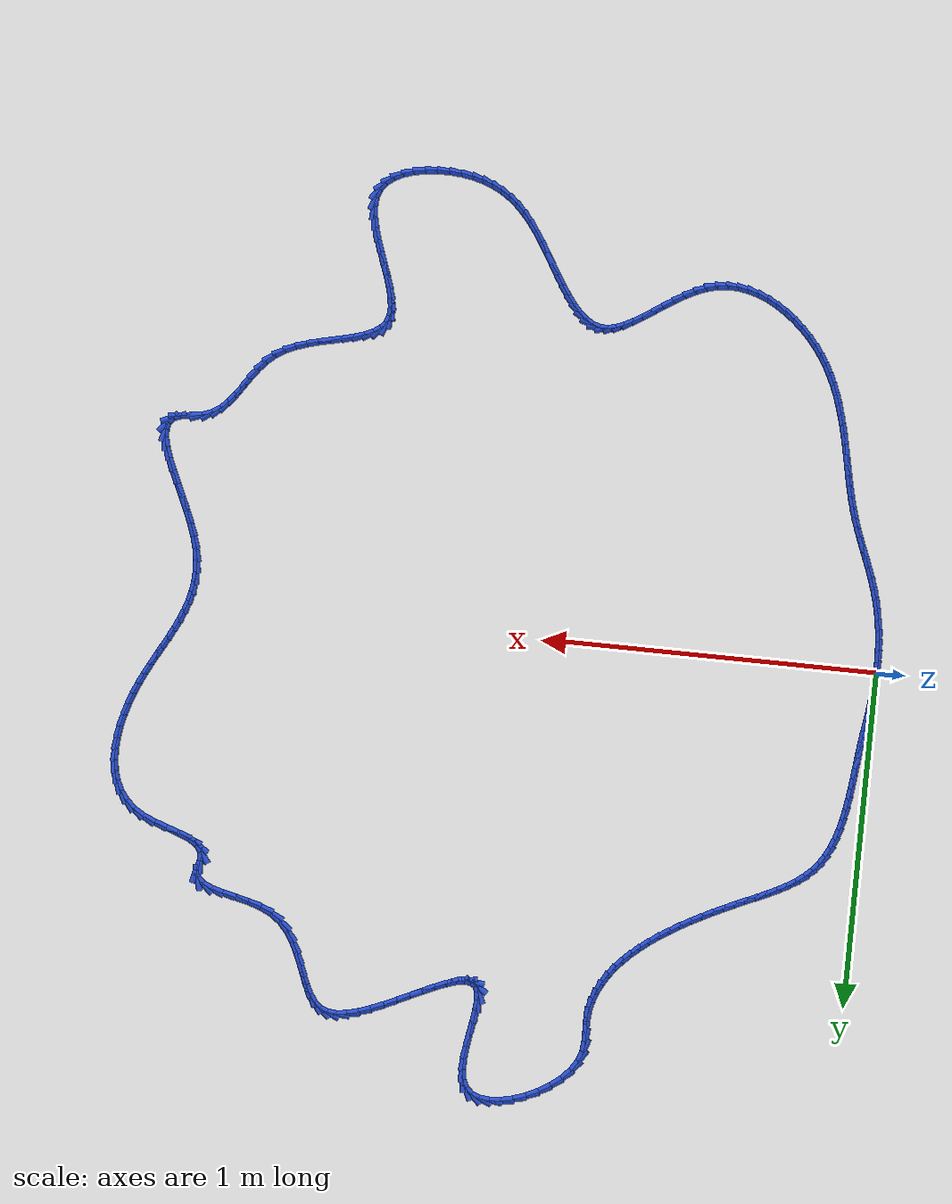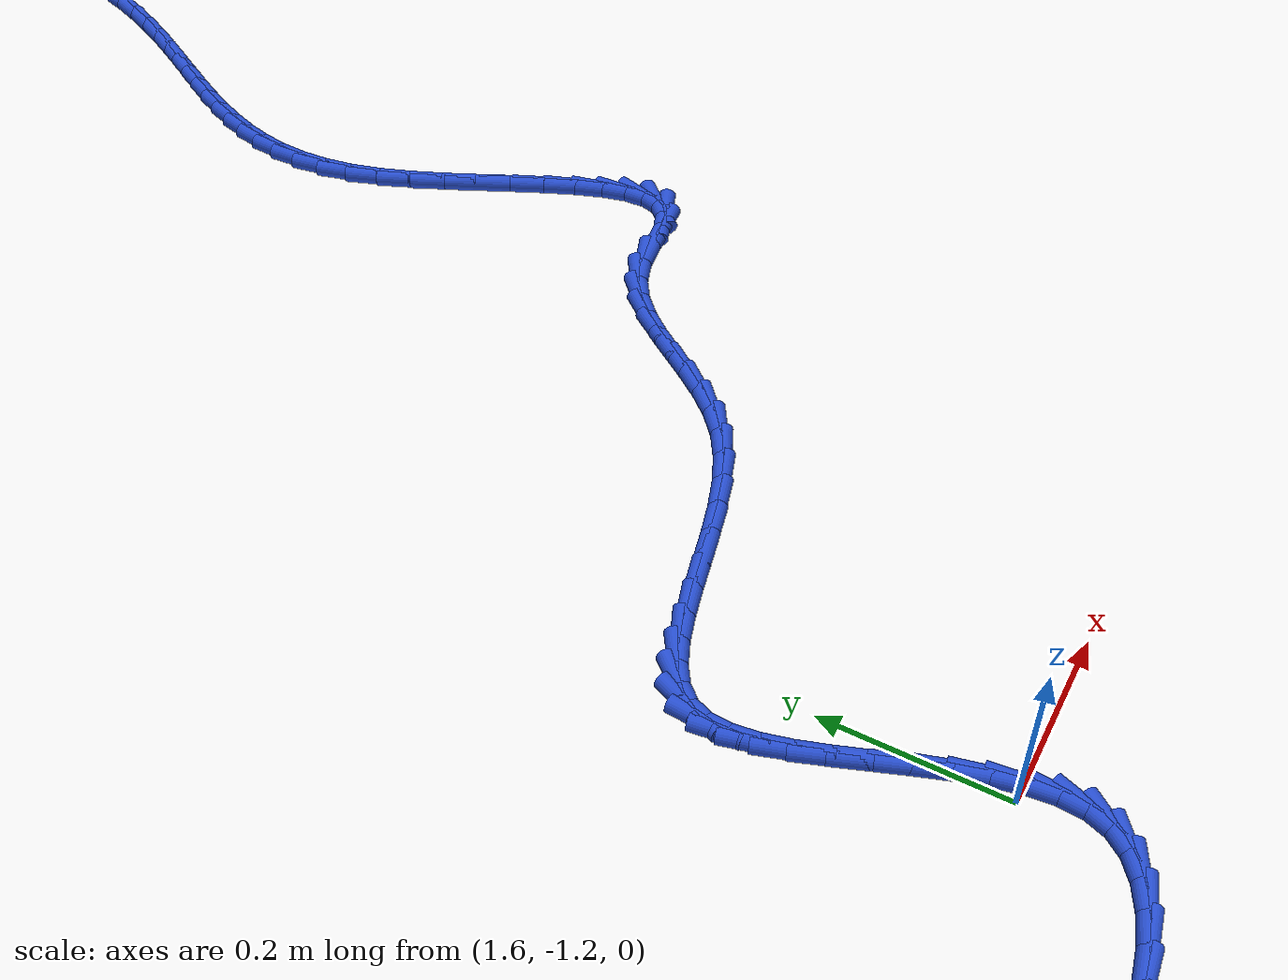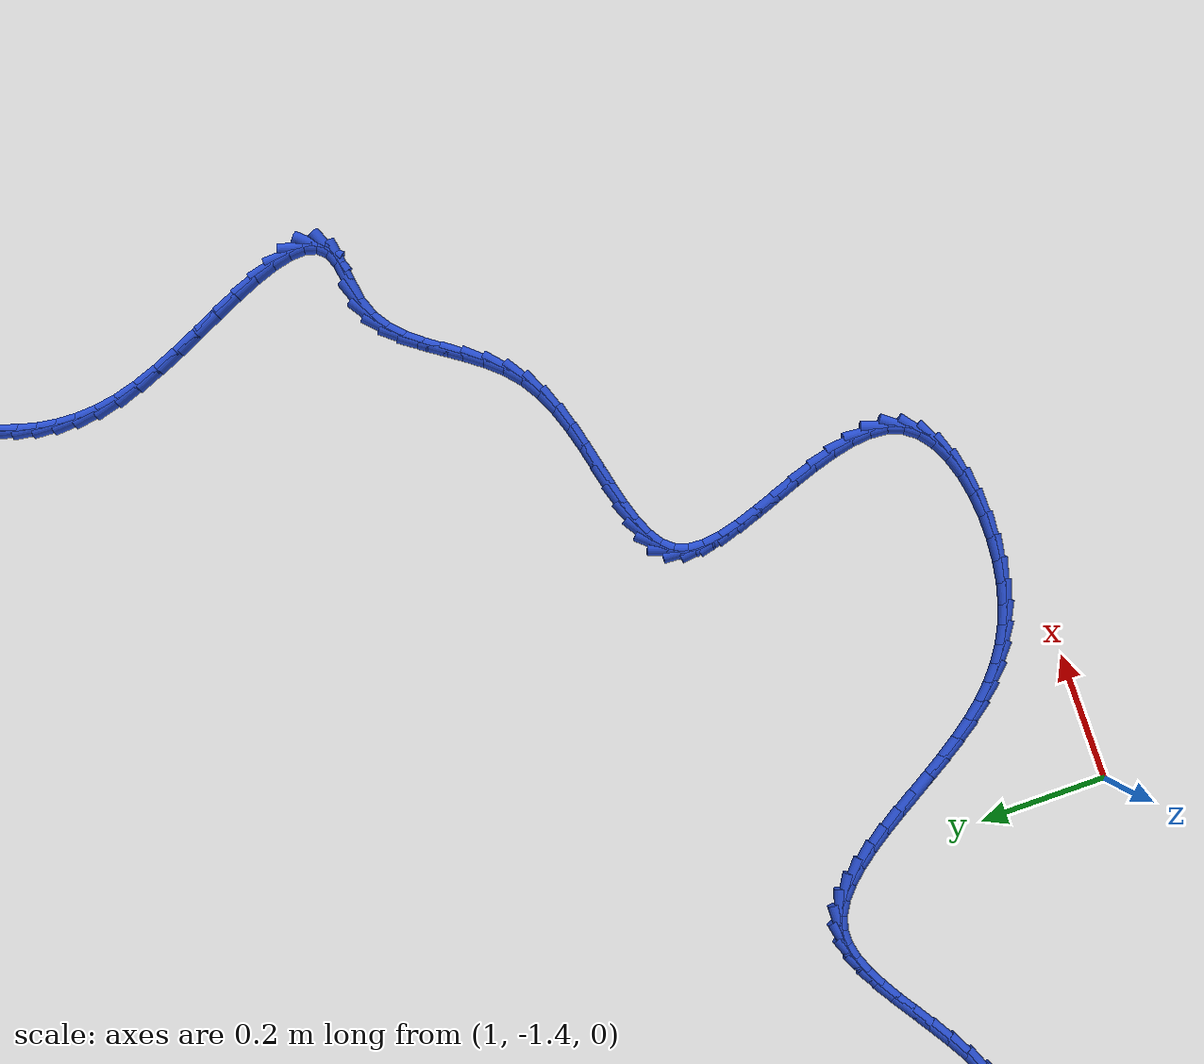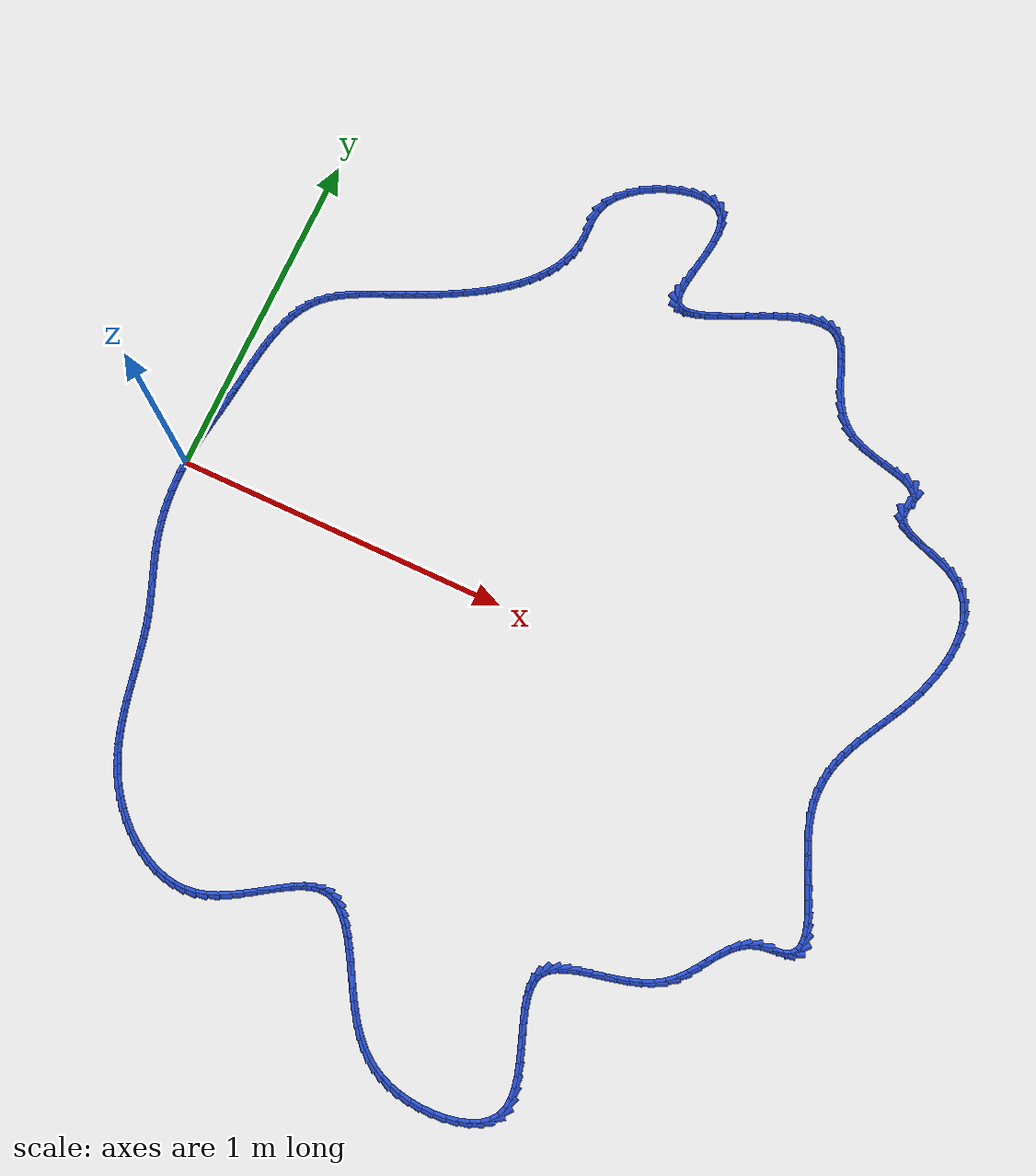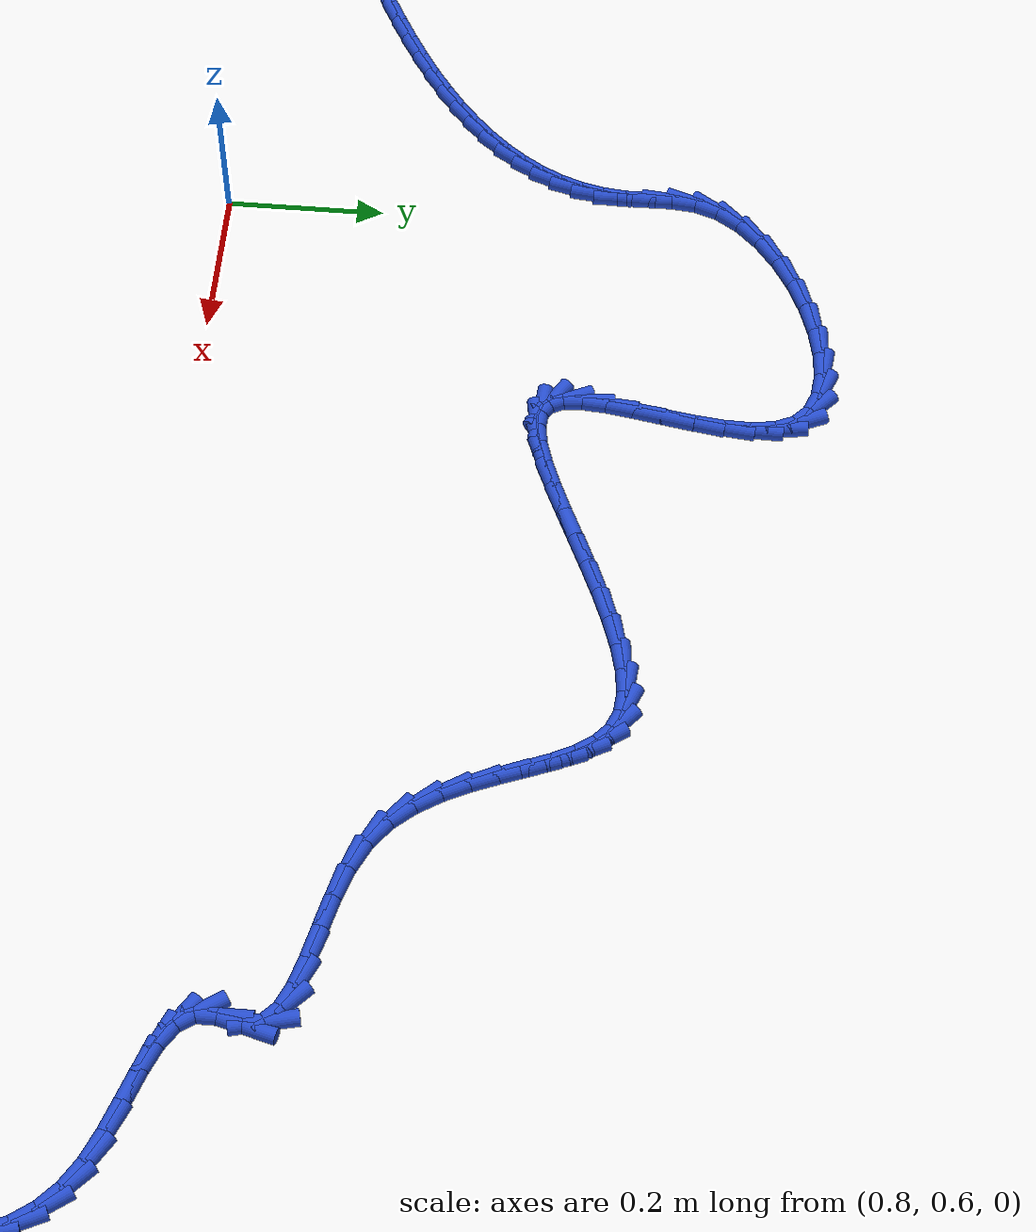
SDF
<sdf version="1.6">
 <world name="default">
  <light name="sun" type="directional">
   <pose>0 0 10 0 -0 0</pose>
   <diffuse>0.8 0.8 0.8 1</diffuse>
   <specular>0.2 0.2 0.2 1</specular>
   <attenuation>
    <range>1000</range>
    <constant>0.9</constant>
    <linear>0.01</linear>
    <quadratic>0.001</quadratic>
   </attenuation>
   <direction>-0.5 0.1 -0.9</direction>
  </light>
  <model name="ground_plane">
   <static>1</static>
   <link name="link">
    <collision name="collision">
     <geometry><plane><normal>0 0 1</normal><size>100 100</size></plane></geometry>
     <surface><friction><ode><mu>100</mu><mu2>50</mu2></ode></friction></surface>
    </collision>
    <visual name="visual">
     <cast_shadows>0</cast_shadows>
     <geometry><plane><normal>0 0 1</normal><size>100 100</size></plane></geometry>
     <material>
      <script><uri>file://media/materials/scripts/gazebo.material</uri><name>Gazebo/WhiteGlow</name></script>
     </material>
    </visual>
   </link>
  </model>
  <gravity>0 0 -9.8</gravity>
  <magnetic_field>6e-06 2.3e-05 -4.2e-05</magnetic_field>
  <atmosphere type="adiabatic"/>
  <physics name="default_physics" default="0" type="ode">
   <max_step_size>0.001</max_step_size>
   <real_time_factor>1</real_time_factor>
   <real_time_update_rate>1000</real_time_update_rate>
  </physics>
  <scene><ambient>0.4 0.4 0.4 1</ambient><background>0.7 0.7 0.7 1</background><shadows>1</shadows></scene>
  <spherical_coordinates>
   <surface_model>EARTH_WGS84</surface_model>
   <latitude_deg>0</latitude_deg>
   <longitude_deg>0</longitude_deg>
   <elevation>0</elevation>
   <heading_deg>0</heading_deg>
  </spherical_coordinates>
  <model name="line">
   <link name="link_0">
    <pose>3.469446951953614e-18 6.938893903907228e-17 0.01 0 1.57 1.5148359961722635</pose>
    <collision name="collision">
     <geometry><cylinder><radius>0.01</radius><length>0.08</length></cylinder></geometry>
    </collision>
    <visual name="visual">
     <material>
      <script><name>Gazebo/Blue</name><uri>file://media/materials/scripts/gazebo.material</uri></script>
     </material>
     <geometry><cylinder><radius>0.01</radius><length>0.08</length></cylinder></geometry>
    </visual>
   </link>
   <link name="link_1">
    <pose>0.0017094850897031327 0.03051626477430296 0.01 0 1.57 1.4822787442814584</pose>
    <collision name="collision">
     <geometry><cylinder><radius>0.01</radius><length>0.08</length></cylinder></geometry>
    </collision>
    <visual name="visual">
     <material>
      <script><name>Gazebo/Blue</name><uri>file://media/materials/scripts/gazebo.material</uri></script>
     </material>
     <geometry><cylinder><radius>0.01</radius><length>0.08</length></cylinder></geometry>
    </visual>
   </link>
   <link name="link_2">
    <pose>0.004403127142022116 0.0608673326392885 0.01 0 1.57 1.4572416024382149</pose>
    <collision name="collision">
     <geometry><cylinder><radius>0.01</radius><length>0.08</length></cylinder></geometry>
    </collision>
    <visual name="visual">
     <material>
      <script><name>Gazebo/Blue</name><uri>file://media/materials/scripts/gazebo.material</uri></script>
     </material>
     <geometry><cylinder><radius>0.01</radius><length>0.08</length></cylinder></geometry>
    </visual>
   </link>
   <link name="link_3">
    <pose>0.007860565706996987 0.09118368402272538 0.01 0 1.57 1.4399921863272171</pose>
    <collision name="collision">
     <geometry><cylinder><radius>0.01</radius><length>0.08</length></cylinder></geometry>
    </collision>
    <visual name="visual">
     <material>
      <script><name>Gazebo/Blue</name><uri>file://media/materials/scripts/gazebo.material</uri></script>
     </material>
     <geometry><cylinder><radius>0.01</radius><length>0.08</length></cylinder></geometry>
    </visual>
   </link>
   <link name="link_4">
    <pose>0.011861440334667765 0.1215957993523822 0.01 0 1.57 1.4305936068685523</pose>
    <collision name="collision">
     <geometry><cylinder><radius>0.01</radius><length>0.08</length></cylinder></geometry>
    </collision>
    <visual name="visual">
     <material>
      <script><name>Gazebo/Blue</name><uri>file://media/materials/scripts/gazebo.material</uri></script>
     </material>
     <geometry><cylinder><radius>0.01</radius><length>0.08</length></cylinder></geometry>
    </visual>
   </link>
   <link name="link_5">
    <pose>0.016185390575074485 0.15223415905602775 0.01 0 1.57 1.428937334421257</pose>
    <collision name="collision">
     <geometry><cylinder><radius>0.01</radius><length>0.08</length></cylinder></geometry>
    </collision>
    <visual name="visual">
     <material>
      <script><name>Gazebo/Blue</name><uri>file://media/materials/scripts/gazebo.material</uri></script>
     </material>
     <geometry><cylinder><radius>0.01</radius><length>0.08</length></cylinder></geometry>
    </visual>
   </link>
   <link name="link_6">
    <pose>0.02061205597825718 0.18322924356143067 0.01 0 1.57 1.4347703071194566</pose>
    <collision name="collision">
     <geometry><cylinder><radius>0.01</radius><length>0.08</length></cylinder></geometry>
    </collision>
    <visual name="visual">
     <material>
      <script><name>Gazebo/Blue</name><uri>file://media/materials/scripts/gazebo.material</uri></script>
     </material>
     <geometry><cylinder><radius>0.01</radius><length>0.08</length></cylinder></geometry>
    </visual>
   </link>
   <link name="link_7">
    <pose>0.024921076094255874 0.21471153329635967 0.01 0 1.57 1.4473631428586085</pose>
    <collision name="collision">
     <geometry><cylinder><radius>0.01</radius><length>0.08</length></cylinder></geometry>
    </collision>
    <visual name="visual">
     <material>
      <script><name>Gazebo/Blue</name><uri>file://media/materials/scripts/gazebo.material</uri></script>
     </material>
     <geometry><cylinder><radius>0.01</radius><length>0.08</length></cylinder></geometry>
    </visual>
   </link>
   <link name="link_8">
    <pose>0.028902506885221817 0.24680331014053886 0.01 0 1.57 1.458472247931736</pose>
    <collision name="collision">
     <geometry><cylinder><radius>0.01</radius><length>0.08</length></cylinder></geometry>
    </collision>
    <visual name="visual">
     <material>
      <script><name>Gazebo/Blue</name><uri>file://media/materials/scripts/gazebo.material</uri></script>
     </material>
     <geometry><cylinder><radius>0.01</radius><length>0.08</length></cylinder></geometry>
    </visual>
   </link>
   <link name="link_9">
    <pose>0.03258388182388039 0.27943994221114893 0.01 0 1.57 1.4605535143209447</pose>
    <collision name="collision">
     <geometry><cylinder><radius>0.01</radius><length>0.08</length></cylinder></geometry>
    </collision>
    <visual name="visual">
     <material>
      <script><name>Gazebo/Blue</name><uri>file://media/materials/scripts/gazebo.material</uri></script>
     </material>
     <geometry><cylinder><radius>0.01</radius><length>0.08</length></cylinder></geometry>
    </visual>
   </link>
   <link name="link_10">
    <pose>0.0362290510704087 0.31237079752331115 0.01 0 1.57 1.4535501227774712</pose>
    <collision name="collision">
     <geometry><cylinder><radius>0.01</radius><length>0.08</length></cylinder></geometry>
    </collision>
    <visual name="visual">
     <material>
      <script><name>Gazebo/Blue</name><uri>file://media/materials/scripts/gazebo.material</uri></script>
     </material>
     <geometry><cylinder><radius>0.01</radius><length>0.08</length></cylinder></geometry>
    </visual>
   </link>
   <link name="link_11">
    <pose>0.04011204903072314 0.34533722827757507 0.01 0 1.57 1.4373722913775842</pose>
    <collision name="collision">
     <geometry><cylinder><radius>0.01</radius><length>0.08</length></cylinder></geometry>
    </collision>
    <visual name="visual">
     <material>
      <script><name>Gazebo/Blue</name><uri>file://media/materials/scripts/gazebo.material</uri></script>
     </material>
     <geometry><cylinder><radius>0.01</radius><length>0.08</length></cylinder></geometry>
    </visual>
   </link>
   <link name="link_12">
    <pose>0.04450691011074005 0.37808058667448996 0.01 0 1.57 1.4115700109490243</pose>
    <collision name="collision">
     <geometry><cylinder><radius>0.01</radius><length>0.08</length></cylinder></geometry>
    </collision>
    <visual name="visual">
     <material>
      <script><name>Gazebo/Blue</name><uri>file://media/materials/scripts/gazebo.material</uri></script>
     </material>
     <geometry><cylinder><radius>0.01</radius><length>0.08</length></cylinder></geometry>
    </visual>
   </link>
   <link name="link_13">
    <pose>0.04968766871637582 0.41034222491460537 0.01 0 1.57 1.3753404858170684</pose>
    <collision name="collision">
     <geometry><cylinder><radius>0.01</radius><length>0.08</length></cylinder></geometry>
    </collision>
    <visual name="visual">
     <material>
      <script><name>Gazebo/Blue</name><uri>file://media/materials/scripts/gazebo.material</uri></script>
     </material>
     <geometry><cylinder><radius>0.01</radius><length>0.08</length></cylinder></geometry>
    </visual>
   </link>
   <link name="link_14">
    <pose>0.05592835925354684 0.4418634951984708 0.01 0 1.57 1.3275423317986499</pose>
    <collision name="collision">
     <geometry><cylinder><radius>0.01</radius><length>0.08</length></cylinder></geometry>
    </collision>
    <visual name="visual">
     <material>
      <script><name>Gazebo/Blue</name><uri>file://media/materials/scripts/gazebo.material</uri></script>
     </material>
     <geometry><cylinder><radius>0.01</radius><length>0.08</length></cylinder></geometry>
    </visual>
   </link>
   <link name="link_15">
    <pose>0.06350301612816944 0.4723857497266353 0.01 0 1.57 1.2667453190669147</pose>
    <collision name="collision">
     <geometry><cylinder><radius>0.01</radius><length>0.08</length></cylinder></geometry>
    </collision>
    <visual name="visual">
     <material>
      <script><name>Gazebo/Blue</name><uri>file://media/materials/scripts/gazebo.material</uri></script>
     </material>
     <geometry><cylinder><radius>0.01</radius><length>0.08</length></cylinder></geometry>
    </visual>
   </link>
   <link name="link_16">
    <pose>0.07268567374616003 0.5016503406996488 0.01 0 1.57 1.1913659395530691</pose>
    <collision name="collision">
     <geometry><cylinder><radius>0.01</radius><length>0.08</length></cylinder></geometry>
    </collision>
    <visual name="visual">
     <material>
      <script><name>Gazebo/Blue</name><uri>file://media/materials/scripts/gazebo.material</uri></script>
     </material>
     <geometry><cylinder><radius>0.01</radius><length>0.08</length></cylinder></geometry>
    </visual>
   </link>
   <link name="link_17">
    <pose>0.08375036651343498 0.5293986203180603 0.01 0 1.57 1.0999642037363957</pose>
    <collision name="collision">
     <geometry><cylinder><radius>0.01</radius><length>0.08</length></cylinder></geometry>
    </collision>
    <visual name="visual">
     <material>
      <script><name>Gazebo/Blue</name><uri>file://media/materials/scripts/gazebo.material</uri></script>
     </material>
     <geometry><cylinder><radius>0.01</radius><length>0.08</length></cylinder></geometry>
    </visual>
   </link>
   <link name="link_18">
    <pose>0.0969711288359106 0.5553719407824192 0.01 0 1.57 0.9917812656120157</pose>
    <collision name="collision">
     <geometry><cylinder><radius>0.01</radius><length>0.08</length></cylinder></geometry>
    </collision>
    <visual name="visual">
     <material>
      <script><name>Gazebo/Blue</name><uri>file://media/materials/scripts/gazebo.material</uri></script>
     </material>
     <geometry><cylinder><radius>0.01</radius><length>0.08</length></cylinder></geometry>
    </visual>
   </link>
   <link name="link_19">
    <pose>0.11262199511950335 0.5793116542932754 0.01 0 1.57 0.8679224436490507</pose>
    <collision name="collision">
     <geometry><cylinder><radius>0.01</radius><length>0.08</length></cylinder></geometry>
    </collision>
    <visual name="visual">
     <material>
      <script><name>Gazebo/Blue</name><uri>file://media/materials/scripts/gazebo.material</uri></script>
     </material>
     <geometry><cylinder><radius>0.01</radius><length>0.08</length></cylinder></geometry>
    </visual>
   </link>
   <link name="link_20">
    <pose>0.1309692275656516 0.6009676379139176 0.01 0 1.57 0.7444854785448493</pose>
    <collision name="collision">
     <geometry><cylinder><radius>0.01</radius><length>0.08</length></cylinder></geometry>
    </collision>
    <visual name="visual">
     <material>
      <script><name>Gazebo/Blue</name><uri>file://media/materials/scripts/gazebo.material</uri></script>
     </material>
     <geometry><cylinder><radius>0.01</radius><length>0.08</length></cylinder></geometry>
    </visual>
   </link>
   <link name="link_21">
    <pose>0.15202555442540144 0.6203678548199021 0.01 0 1.57 0.64076058064986</pose>
    <collision name="collision">
     <geometry><cylinder><radius>0.01</radius><length>0.08</length></cylinder></geometry>
    </collision>
    <visual name="visual">
     <material>
      <script><name>Gazebo/Blue</name><uri>file://media/materials/scripts/gazebo.material</uri></script>
     </material>
     <geometry><cylinder><radius>0.01</radius><length>0.08</length></cylinder></geometry>
    </visual>
   </link>
   <link name="link_22">
    <pose>0.17550000388395723 0.6378733784880832 0.01 0 1.57 0.5586481810111097</pose>
    <collision name="collision">
     <geometry><cylinder><radius>0.01</radius><length>0.08</length></cylinder></geometry>
    </collision>
    <visual name="visual">
     <material>
      <script><name>Gazebo/Blue</name><uri>file://media/materials/scripts/gazebo.material</uri></script>
     </material>
     <geometry><cylinder><radius>0.01</radius><length>0.08</length></cylinder></geometry>
    </visual>
   </link>
   <link name="link_23">
    <pose>0.20108369606787138 0.6538649246657148 0.01 0 1.57 0.49713551053261557</pose>
    <collision name="collision">
     <geometry><cylinder><radius>0.01</radius><length>0.08</length></cylinder></geometry>
    </collision>
    <visual name="visual">
     <material>
      <script><name>Gazebo/Blue</name><uri>file://media/materials/scripts/gazebo.material</uri></script>
     </material>
     <geometry><cylinder><radius>0.01</radius><length>0.08</length></cylinder></geometry>
    </visual>
   </link>
   <link name="link_24">
    <pose>0.22846775110369635 0.6687232091000502 0.01 0 1.57 0.45440642235736683</pose>
    <collision name="collision">
     <geometry><cylinder><radius>0.01</radius><length>0.08</length></cylinder></geometry>
    </collision>
    <visual name="visual">
     <material>
      <script><name>Gazebo/Blue</name><uri>file://media/materials/scripts/gazebo.material</uri></script>
     </material>
     <geometry><cylinder><radius>0.01</radius><length>0.08</length></cylinder></geometry>
    </visual>
   </link>
   <link name="link_25">
    <pose>0.25734328911798443 0.6828289475383432 0.01 0 1.57 0.42858658572058783</pose>
    <collision name="collision">
     <geometry><cylinder><radius>0.01</radius><length>0.08</length></cylinder></geometry>
    </collision>
    <visual name="visual">
     <material>
      <script><name>Gazebo/Blue</name><uri>file://media/materials/scripts/gazebo.material</uri></script>
     </material>
     <geometry><cylinder><radius>0.01</radius><length>0.08</length></cylinder></geometry>
    </visual>
   </link>
   <link name="link_26">
    <pose>0.2874014302372878 0.6965628557278467 0.01 0 1.57 0.41809739632010245</pose>
    <collision name="collision">
     <geometry><cylinder><radius>0.01</radius><length>0.08</length></cylinder></geometry>
    </collision>
    <visual name="visual">
     <material>
      <script><name>Gazebo/Blue</name><uri>file://media/materials/scripts/gazebo.material</uri></script>
     </material>
     <geometry><cylinder><radius>0.01</radius><length>0.08</length></cylinder></geometry>
    </visual>
   </link>
   <link name="link_27">
    <pose>0.3183332945881591 0.7103056494158148 0.01 0 1.57 0.42150549893042916</pose>
    <collision name="collision">
     <geometry><cylinder><radius>0.01</radius><length>0.08</length></cylinder></geometry>
    </collision>
    <visual name="visual">
     <material>
      <script><name>Gazebo/Blue</name><uri>file://media/materials/scripts/gazebo.material</uri></script>
     </material>
     <geometry><cylinder><radius>0.01</radius><length>0.08</length></cylinder></geometry>
    </visual>
   </link>
   <link name="link_28">
    <pose>0.34983224440703614 0.7244291327424857 0.01 0 1.57 0.4329973155200589</pose>
    <collision name="collision">
     <geometry><cylinder><radius>0.01</radius><length>0.08</length></cylinder></geometry>
    </collision>
    <visual name="visual">
     <material>
      <script><name>Gazebo/Blue</name><uri>file://media/materials/scripts/gazebo.material</uri></script>
     </material>
     <geometry><cylinder><radius>0.01</radius><length>0.08</length></cylinder></geometry>
    </visual>
   </link>
   <link name="link_29">
    <pose>0.38163560851254097 0.7391303579749843 0.01 0 1.57 0.4478171561913903</pose>
    <collision name="collision">
     <geometry><cylinder><radius>0.01</radius><length>0.08</length></cylinder></geometry>
    </collision>
    <visual name="visual">
     <material>
      <script><name>Gazebo/Blue</name><uri>file://media/materials/scripts/gazebo.material</uri></script>
     </material>
     <geometry><cylinder><radius>0.01</radius><length>0.08</length></cylinder></geometry>
    </visual>
   </link>
   <link name="link_30">
    <pose>0.4135208327494134 0.754446926153856 0.01 0 1.57 0.46592984751644967</pose>
    <collision name="collision">
     <geometry><cylinder><radius>0.01</radius><length>0.08</length></cylinder></geometry>
    </collision>
    <visual name="visual">
     <material>
      <script><name>Gazebo/Blue</name><uri>file://media/materials/scripts/gazebo.material</uri></script>
     </material>
     <geometry><cylinder><radius>0.01</radius><length>0.08</length></cylinder></geometry>
    </visual>
   </link>
   <link name="link_31">
    <pose>0.44526683313413923 0.7704105948982635 0.01 0 1.57 0.4875602864950086</pose>
    <collision name="collision">
     <geometry><cylinder><radius>0.01</radius><length>0.08</length></cylinder></geometry>
    </collision>
    <visual name="visual">
     <material>
      <script><name>Gazebo/Blue</name><uri>file://media/materials/scripts/gazebo.material</uri></script>
     </material>
     <geometry><cylinder><radius>0.01</radius><length>0.08</length></cylinder></geometry>
    </visual>
   </link>
   <link name="link_32">
    <pose>0.4766525256832046 0.7870531218273707 0.01 0 1.57 0.5130235854854662</pose>
    <collision name="collision">
     <geometry><cylinder><radius>0.01</radius><length>0.08</length></cylinder></geometry>
    </collision>
    <visual name="visual">
     <material>
      <script><name>Gazebo/Blue</name><uri>file://media/materials/scripts/gazebo.material</uri></script>
     </material>
     <geometry><cylinder><radius>0.01</radius><length>0.08</length></cylinder></geometry>
    </visual>
   </link>
   <link name="link_33">
    <pose>0.5074568264130951 0.8044062645603404 0.01 0 1.57 0.5427303918857371</pose>
    <collision name="collision">
     <geometry><cylinder><radius>0.01</radius><length>0.08</length></cylinder></geometry>
    </collision>
    <visual name="visual">
     <material>
      <script><name>Gazebo/Blue</name><uri>file://media/materials/scripts/gazebo.material</uri></script>
     </material>
     <geometry><cylinder><radius>0.01</radius><length>0.08</length></cylinder></geometry>
    </visual>
   </link>
   <link name="link_34">
    <pose>0.5374586513402968 0.8225017807163357 0.01 0 1.57 0.5771941331386569</pose>
    <collision name="collision">
     <geometry><cylinder><radius>0.01</radius><length>0.08</length></cylinder></geometry>
    </collision>
    <visual name="visual">
     <material>
      <script><name>Gazebo/Blue</name><uri>file://media/materials/scripts/gazebo.material</uri></script>
     </material>
     <geometry><cylinder><radius>0.01</radius><length>0.08</length></cylinder></geometry>
    </visual>
   </link>
   <link name="link_35">
    <pose>0.5664369164812953 0.8413714279145198 0.01 0 1.57 0.6170381671087958</pose>
    <collision name="collision">
     <geometry><cylinder><radius>0.01</radius><length>0.08</length></cylinder></geometry>
    </collision>
    <visual name="visual">
     <material>
      <script><name>Gazebo/Blue</name><uri>file://media/materials/scripts/gazebo.material</uri></script>
     </material>
     <geometry><cylinder><radius>0.01</radius><length>0.08</length></cylinder></geometry>
    </visual>
   </link>
   <link name="link_36">
    <pose>0.5941705378525772 0.8610469637740563 0.01 0 1.57 0.6629994227871604</pose>
    <collision name="collision">
     <geometry><cylinder><radius>0.01</radius><length>0.08</length></cylinder></geometry>
    </collision>
    <visual name="visual">
     <material>
      <script><name>Gazebo/Blue</name><uri>file://media/materials/scripts/gazebo.material</uri></script>
     </material>
     <geometry><cylinder><radius>0.01</radius><length>0.08</length></cylinder></geometry>
    </visual>
   </link>
   <link name="link_37">
    <pose>0.6204384314706277 0.8815601459141077 0.01 0 1.57 0.7159226816246992</pose>
    <collision name="collision">
     <geometry><cylinder><radius>0.01</radius><length>0.08</length></cylinder></geometry>
    </collision>
    <visual name="visual">
     <material>
      <script><name>Gazebo/Blue</name><uri>file://media/materials/scripts/gazebo.material</uri></script>
     </material>
     <geometry><cylinder><radius>0.01</radius><length>0.08</length></cylinder></geometry>
    </visual>
   </link>
   <link name="link_38">
    <pose>0.6450195133519329 0.9029427319538376 0.01 0 1.57 0.7767358986538571</pose>
    <collision name="collision">
     <geometry><cylinder><radius>0.01</radius><length>0.08</length></cylinder></geometry>
    </collision>
    <visual name="visual">
     <material>
      <script><name>Gazebo/Blue</name><uri>file://media/materials/scripts/gazebo.material</uri></script>
     </material>
     <geometry><cylinder><radius>0.01</radius><length>0.08</length></cylinder></geometry>
    </visual>
   </link>
   <link name="link_39">
    <pose>0.667692699512979 0.9252264795124091 0.01 0 1.57 0.8463920409993408</pose>
    <collision name="collision">
     <geometry><cylinder><radius>0.01</radius><length>0.08</length></cylinder></geometry>
    </collision>
    <visual name="visual">
     <material>
      <script><name>Gazebo/Blue</name><uri>file://media/materials/scripts/gazebo.material</uri></script>
     </material>
     <geometry><cylinder><radius>0.01</radius><length>0.08</length></cylinder></geometry>
    </visual>
   </link>
   <link name="link_40">
    <pose>0.6882369059702512 0.9484431462089848 0.01 0 1.57 0.9257583472496942</pose>
    <collision name="collision">
     <geometry><cylinder><radius>0.01</radius><length>0.08</length></cylinder></geometry>
    </collision>
    <visual name="visual">
     <material>
      <script><name>Gazebo/Blue</name><uri>file://media/materials/scripts/gazebo.material</uri></script>
     </material>
     <geometry><cylinder><radius>0.01</radius><length>0.08</length></cylinder></geometry>
    </visual>
   </link>
   <link name="link_41">
    <pose>0.7064310487402363 0.9726244896627291 0.01 0 1.57 1.0154342378449421</pose>
    <collision name="collision">
     <geometry><cylinder><radius>0.01</radius><length>0.08</length></cylinder></geometry>
    </collision>
    <visual name="visual">
     <material>
      <script><name>Gazebo/Blue</name><uri>file://media/materials/scripts/gazebo.material</uri></script>
     </material>
     <geometry><cylinder><radius>0.01</radius><length>0.08</length></cylinder></geometry>
    </visual>
   </link>
   <link name="link_42">
    <pose>0.7220540438394192 0.9978022674928039 0.01 0 1.57 1.1154934103453327</pose>
    <collision name="collision">
     <geometry><cylinder><radius>0.01</radius><length>0.08</length></cylinder></geometry>
    </collision>
    <visual name="visual">
     <material>
      <script><name>Gazebo/Blue</name><uri>file://media/materials/scripts/gazebo.material</uri></script>
     </material>
     <geometry><cylinder><radius>0.01</radius><length>0.08</length></cylinder></geometry>
    </visual>
   </link>
   <link name="link_43">
    <pose>0.7348848072842867 1.024008237318373 0.01 0 1.57 1.2251850060388396</pose>
    <collision name="collision">
     <geometry><cylinder><radius>0.01</radius><length>0.08</length></cylinder></geometry>
    </collision>
    <visual name="visual">
     <material>
      <script><name>Gazebo/Blue</name><uri>file://media/materials/scripts/gazebo.material</uri></script>
     </material>
     <geometry><cylinder><radius>0.01</radius><length>0.08</length></cylinder></geometry>
    </visual>
   </link>
   <link name="link_44">
    <pose>0.7447022550913243 1.0512741567585997 0.01 0 1.57 1.342692771393778</pose>
    <collision name="collision">
     <geometry><cylinder><radius>0.01</radius><length>0.08</length></cylinder></geometry>
    </collision>
    <visual name="visual">
     <material>
      <script><name>Gazebo/Blue</name><uri>file://media/materials/scripts/gazebo.material</uri></script>
     </material>
     <geometry><cylinder><radius>0.01</radius><length>0.08</length></cylinder></geometry>
    </visual>
   </link>
   <link name="link_45">
    <pose>0.7512853032770179 1.079631783432647 0.01 0 1.57 1.4651045094513409</pose>
    <collision name="collision">
     <geometry><cylinder><radius>0.01</radius><length>0.08</length></cylinder></geometry>
    </collision>
    <visual name="visual">
     <material>
      <script><name>Gazebo/Blue</name><uri>file://media/materials/scripts/gazebo.material</uri></script>
     </material>
     <geometry><cylinder><radius>0.01</radius><length>0.08</length></cylinder></geometry>
    </visual>
   </link>
   <link name="link_46">
    <pose>0.7544128678578532 1.1091128749596777 0.01 0 1.57 -1.565123118664342</pose>
    <collision name="collision">
     <geometry><cylinder><radius>0.01</radius><length>0.08</length></cylinder></geometry>
    </collision>
    <visual name="visual">
     <material>
      <script><name>Gazebo/Blue</name><uri>file://media/materials/scripts/gazebo.material</uri></script>
     </material>
     <geometry><cylinder><radius>0.01</radius><length>0.08</length></cylinder></geometry>
    </visual>
   </link>
   <link name="link_47">
    <pose>0.7542394287900196 1.1396841501728345 0.01 0 1.57 -1.551285245928476</pose>
    <collision name="collision">
     <geometry><cylinder><radius>0.01</radius><length>0.08</length></cylinder></geometry>
    </collision>
    <visual name="visual">
     <material>
      <script><name>Gazebo/Blue</name><uri>file://media/materials/scripts/gazebo.material</uri></script>
     </material>
     <geometry><cylinder><radius>0.01</radius><length>0.08</length></cylinder></geometry>
    </visual>
   </link>
   <link name="link_48">
    <pose>0.7536314149902414 1.1708426825280125 0.01 0 1.57 1.4739614110613546</pose>
    <collision name="collision">
     <geometry><cylinder><radius>0.01</radius><length>0.08</length></cylinder></geometry>
    </collision>
    <visual name="visual">
     <material>
      <script><name>Gazebo/Blue</name><uri>file://media/materials/scripts/gazebo.material</uri></script>
     </material>
     <geometry><cylinder><radius>0.01</radius><length>0.08</length></cylinder></geometry>
    </visual>
   </link>
   <link name="link_49">
    <pose>0.7566462715607866 1.20187928966512 0.01 0 1.57 1.2376302781974073</pose>
    <collision name="collision">
     <geometry><cylinder><radius>0.01</radius><length>0.08</length></cylinder></geometry>
    </collision>
    <visual name="visual">
     <material>
      <script><name>Gazebo/Blue</name><uri>file://media/materials/scripts/gazebo.material</uri></script>
     </material>
     <geometry><cylinder><radius>0.01</radius><length>0.08</length></cylinder></geometry>
    </visual>
   </link>
   <link name="link_50">
    <pose>0.7671012323210288 1.232090157320033 0.01 0 1.57 0.9969393964905722</pose>
    <collision name="collision">
     <geometry><cylinder><radius>0.01</radius><length>0.08</length></cylinder></geometry>
    </collision>
    <visual name="visual">
     <material>
      <script><name>Gazebo/Blue</name><uri>file://media/materials/scripts/gazebo.material</uri></script>
     </material>
     <geometry><cylinder><radius>0.01</radius><length>0.08</length></cylinder></geometry>
    </visual>
   </link>
   <link name="link_51">
    <pose>0.7856929306717021 1.2608510177882872 0.01 0 1.57 0.8135538663231653</pose>
    <collision name="collision">
     <geometry><cylinder><radius>0.01</radius><length>0.08</length></cylinder></geometry>
    </collision>
    <visual name="visual">
     <material>
      <script><name>Gazebo/Blue</name><uri>file://media/materials/scripts/gazebo.material</uri></script>
     </material>
     <geometry><cylinder><radius>0.01</radius><length>0.08</length></cylinder></geometry>
    </visual>
   </link>
   <link name="link_52">
    <pose>0.8109693052200629 1.2875923752860927 0.01 0 1.57 0.6703260207869093</pose>
    <collision name="collision">
     <geometry><cylinder><radius>0.01</radius><length>0.08</length></cylinder></geometry>
    </collision>
    <visual name="visual">
     <material>
      <script><name>Gazebo/Blue</name><uri>file://media/materials/scripts/gazebo.material</uri></script>
     </material>
     <geometry><cylinder><radius>0.01</radius><length>0.08</length></cylinder></geometry>
    </visual>
   </link>
   <link name="link_53">
    <pose>0.8414358769488511 1.311745815288275 0.01 0 1.57 0.5511061789342686</pose>
    <collision name="collision">
     <geometry><cylinder><radius>0.01</radius><length>0.08</length></cylinder></geometry>
    </collision>
    <visual name="visual">
     <material>
      <script><name>Gazebo/Blue</name><uri>file://media/materials/scripts/gazebo.material</uri></script>
     </material>
     <geometry><cylinder><radius>0.01</radius><length>0.08</length></cylinder></geometry>
    </visual>
   </link>
   <link name="link_54">
    <pose>0.8755981668408074 1.332742923269662 0.01 0 1.57 0.44344127174849596</pose>
    <collision name="collision">
     <geometry><cylinder><radius>0.01</radius><length>0.08</length></cylinder></geometry>
    </collision>
    <visual name="visual">
     <material>
      <script><name>Gazebo/Blue</name><uri>file://media/materials/scripts/gazebo.material</uri></script>
     </material>
     <geometry><cylinder><radius>0.01</radius><length>0.08</length></cylinder></geometry>
    </visual>
   </link>
   <link name="link_55">
    <pose>0.9119616958786724 1.3500152847050813 0.01 0 1.57 0.3367853414580079</pose>
    <collision name="collision">
     <geometry><cylinder><radius>0.01</radius><length>0.08</length></cylinder></geometry>
    </collision>
    <visual name="visual">
     <material>
      <script><name>Gazebo/Blue</name><uri>file://media/materials/scripts/gazebo.material</uri></script>
     </material>
     <geometry><cylinder><radius>0.01</radius><length>0.08</length></cylinder></geometry>
    </visual>
   </link>
   <link name="link_56">
    <pose>0.949031985045186 1.3629944850693592 0.01 0 1.57 0.2201085991333209</pose>
    <collision name="collision">
     <geometry><cylinder><radius>0.01</radius><length>0.08</length></cylinder></geometry>
    </collision>
    <visual name="visual">
     <material>
      <script><name>Gazebo/Blue</name><uri>file://media/materials/scripts/gazebo.material</uri></script>
     </material>
     <geometry><cylinder><radius>0.01</radius><length>0.08</length></cylinder></geometry>
    </visual>
   </link>
   <link name="link_57">
    <pose>0.9853145553230893 1.3711121098373238 0.01 0 1.57 0.07888318545375729</pose>
    <collision name="collision">
     <geometry><cylinder><radius>0.01</radius><length>0.08</length></cylinder></geometry>
    </collision>
    <visual name="visual">
     <material>
      <script><name>Gazebo/Blue</name><uri>file://media/materials/scripts/gazebo.material</uri></script>
     </material>
     <geometry><cylinder><radius>0.01</radius><length>0.08</length></cylinder></geometry>
    </visual>
   </link>
   <link name="link_58">
    <pose>1.0193149276951223 1.373799744483802 0.01 0 1.57 -0.10910717446356327</pose>
    <collision name="collision">
     <geometry><cylinder><radius>0.01</radius><length>0.08</length></cylinder></geometry>
    </collision>
    <visual name="visual">
     <material>
      <script><name>Gazebo/Blue</name><uri>file://media/materials/scripts/gazebo.material</uri></script>
     </material>
     <geometry><cylinder><radius>0.01</radius><length>0.08</length></cylinder></geometry>
    </visual>
   </link>
   <link name="link_59">
    <pose>1.0495386231440262 1.3704889744836213 0.01 0 1.57 -0.3769280588828411</pose>
    <collision name="collision">
     <geometry><cylinder><radius>0.01</radius><length>0.08</length></cylinder></geometry>
    </collision>
    <visual name="visual">
     <material>
      <script><name>Gazebo/Blue</name><uri>file://media/materials/scripts/gazebo.material</uri></script>
     </material>
     <geometry><cylinder><radius>0.01</radius><length>0.08</length></cylinder></geometry>
    </visual>
   </link>
   <link name="link_60">
    <pose>1.0744911626525406 1.3606113853116086 0.01 0 1.57 -0.7520310955173655</pose>
    <collision name="collision">
     <geometry><cylinder><radius>0.01</radius><length>0.08</length></cylinder></geometry>
    </collision>
    <visual name="visual">
     <material>
      <script><name>Gazebo/Blue</name><uri>file://media/materials/scripts/gazebo.material</uri></script>
     </material>
     <geometry><cylinder><radius>0.01</radius><length>0.08</length></cylinder></geometry>
    </visual>
   </link>
   <link name="link_61">
    <pose>1.0926785679842412 1.3435989321293988 0.01 0 1.57 -1.1583868694684745</pose>
    <collision name="collision">
     <geometry><cylinder><radius>0.01</radius><length>0.08</length></cylinder></geometry>
    </collision>
    <visual name="visual">
     <material>
      <script><name>Gazebo/Blue</name><uri>file://media/materials/scripts/gazebo.material</uri></script>
     </material>
     <geometry><cylinder><radius>0.01</radius><length>0.08</length></cylinder></geometry>
    </visual>
   </link>
   <link name="link_62">
    <pose>1.1032755446283458 1.3193772063051687 0.01 0 1.57 -1.4328693255674418</pose>
    <collision name="collision">
     <geometry><cylinder><radius>0.01</radius><length>0.08</length></cylinder></geometry>
    </collision>
    <visual name="visual">
     <material>
      <script><name>Gazebo/Blue</name><uri>file://media/materials/scripts/gazebo.material</uri></script>
     </material>
     <geometry><cylinder><radius>0.01</radius><length>0.08</length></cylinder></geometry>
    </visual>
   </link>
   <link name="link_63">
    <pose>1.1074450222640044 1.2893395475748737 0.01 0 1.57 1.549528040054991</pose>
    <collision name="collision">
     <geometry><cylinder><radius>0.01</radius><length>0.08</length></cylinder></geometry>
    </collision>
    <visual name="visual">
     <material>
      <script><name>Gazebo/Blue</name><uri>file://media/materials/scripts/gazebo.material</uri></script>
     </material>
     <geometry><cylinder><radius>0.01</radius><length>0.08</length></cylinder></geometry>
    </visual>
   </link>
   <link name="link_64">
    <pose>1.1067177775396946 1.2551508479428495 0.01 0 1.57 1.4596487356431156</pose>
    <collision name="collision">
     <geometry><cylinder><radius>0.01</radius><length>0.08</length></cylinder></geometry>
    </collision>
    <visual name="visual">
     <material>
      <script><name>Gazebo/Blue</name><uri>file://media/materials/scripts/gazebo.material</uri></script>
     </material>
     <geometry><cylinder><radius>0.01</radius><length>0.08</length></cylinder></geometry>
    </visual>
   </link>
   <link name="link_65">
    <pose>1.1026245871038927 1.218475999413431 0.01 0 1.57 1.4139883255677506</pose>
    <collision name="collision">
     <geometry><cylinder><radius>0.01</radius><length>0.08</length></cylinder></geometry>
    </collision>
    <visual name="visual">
     <material>
      <script><name>Gazebo/Blue</name><uri>file://media/materials/scripts/gazebo.material</uri></script>
     </material>
     <geometry><cylinder><radius>0.01</radius><length>0.08</length></cylinder></geometry>
    </visual>
   </link>
   <link name="link_66">
    <pose>1.0966962276050753 1.1809798939909537 0.01 0 1.57 1.4023575920434987</pose>
    <collision name="collision">
     <geometry><cylinder><radius>0.01</radius><length>0.08</length></cylinder></geometry>
    </collision>
    <visual name="visual">
     <material>
      <script><name>Gazebo/Blue</name><uri>file://media/materials/scripts/gazebo.material</uri></script>
     </material>
     <geometry><cylinder><radius>0.01</radius><length>0.08</length></cylinder></geometry>
    </visual>
   </link>
   <link name="link_67">
    <pose>1.0904634756917202 1.1443274236797534 0.01 0 1.57 1.4252083914165583</pose>
    <collision name="collision">
     <geometry><cylinder><radius>0.01</radius><length>0.08</length></cylinder></geometry>
    </collision>
    <visual name="visual">
     <material>
      <script><name>Gazebo/Blue</name><uri>file://media/materials/scripts/gazebo.material</uri></script>
     </material>
     <geometry><cylinder><radius>0.01</radius><length>0.08</length></cylinder></geometry>
    </visual>
   </link>
   <link name="link_68">
    <pose>1.0854571080123032 1.110183480484164 0.01 0 1.57 1.4958894476220779</pose>
    <collision name="collision">
     <geometry><cylinder><radius>0.01</radius><length>0.08</length></cylinder></geometry>
    </collision>
    <visual name="visual">
     <material>
      <script><name>Gazebo/Blue</name><uri>file://media/materials/scripts/gazebo.material</uri></script>
     </material>
     <geometry><cylinder><radius>0.01</radius><length>0.08</length></cylinder></geometry>
    </visual>
   </link>
   <link name="link_69">
    <pose>1.083207901215302 1.0802129564085219 0.01 0 1.57 -1.4865147421079121</pose>
    <collision name="collision">
     <geometry><cylinder><radius>0.01</radius><length>0.08</length></cylinder></geometry>
    </collision>
    <visual name="visual">
     <material>
      <script><name>Gazebo/Blue</name><uri>file://media/materials/scripts/gazebo.material</uri></script>
     </material>
     <geometry><cylinder><radius>0.01</radius><length>0.08</length></cylinder></geometry>
    </visual>
   </link>
   <link name="link_70">
    <pose>1.0852466319491936 1.0560807434571624 0.01 0 1.57 -1.131106478545082</pose>
    <collision name="collision">
     <geometry><cylinder><radius>0.01</radius><length>0.08</length></cylinder></geometry>
    </collision>
    <visual name="visual">
     <material>
      <script><name>Gazebo/Blue</name><uri>file://media/materials/scripts/gazebo.material</uri></script>
     </material>
     <geometry><cylinder><radius>0.01</radius><length>0.08</length></cylinder></geometry>
    </visual>
   </link>
   <link name="link_71">
    <pose>1.0930815604191333 1.039424917963502 0.01 0 1.57 -0.547721271546958</pose>
    <collision name="collision">
     <geometry><cylinder><radius>0.01</radius><length>0.08</length></cylinder></geometry>
    </collision>
    <visual name="visual">
     <material>
      <script><name>Gazebo/Blue</name><uri>file://media/materials/scripts/gazebo.material</uri></script>
     </material>
     <geometry><cylinder><radius>0.01</radius><length>0.08</length></cylinder></geometry>
    </visual>
   </link>
   <link name="link_72">
    <pose>1.107280714808188 1.0307637989293044 0.01 0 1.57 -0.08279852546865821</pose>
    <collision name="collision">
     <geometry><cylinder><radius>0.01</radius><length>0.08</length></cylinder></geometry>
    </collision>
    <visual name="visual">
     <material>
      <script><name>Gazebo/Blue</name><uri>file://media/materials/scripts/gazebo.material</uri></script>
     </material>
     <geometry><cylinder><radius>0.01</radius><length>0.08</length></cylinder></geometry>
    </visual>
   </link>
   <link name="link_73">
    <pose>1.1271517943528981 1.0291147326761743 0.01 0 1.57 0.17096384687964966</pose>
    <collision name="collision">
     <geometry><cylinder><radius>0.01</radius><length>0.08</length></cylinder></geometry>
    </collision>
    <visual name="visual">
     <material>
      <script><name>Gazebo/Blue</name><uri>file://media/materials/scripts/gazebo.material</uri></script>
     </material>
     <geometry><cylinder><radius>0.01</radius><length>0.08</length></cylinder></geometry>
    </visual>
   </link>
   <link name="link_74">
    <pose>1.1519142346142703 1.0333899490273684 0.01 0 1.57 0.3056856345329345</pose>
    <collision name="collision">
     <geometry><cylinder><radius>0.01</radius><length>0.08</length></cylinder></geometry>
    </collision>
    <visual name="visual">
     <material>
      <script><name>Gazebo/Blue</name><uri>file://media/materials/scripts/gazebo.material</uri></script>
     </material>
     <geometry><cylinder><radius>0.01</radius><length>0.08</length></cylinder></geometry>
    </visual>
   </link>
   <link name="link_75">
    <pose>1.1807874711533108 1.0425016778061411 0.01 0 1.57 0.3799463334285185</pose>
    <collision name="collision">
     <geometry><cylinder><radius>0.01</radius><length>0.08</length></cylinder></geometry>
    </collision>
    <visual name="visual">
     <material>
      <script><name>Gazebo/Blue</name><uri>file://media/materials/scripts/gazebo.material</uri></script>
     </material>
     <geometry><cylinder><radius>0.01</radius><length>0.08</length></cylinder></geometry>
    </visual>
   </link>
   <link name="link_76">
    <pose>1.212990939531026 1.055362148835749 0.01 0 1.57 0.42003950544704977</pose>
    <collision name="collision">
     <geometry><cylinder><radius>0.01</radius><length>0.08</length></cylinder></geometry>
    </collision>
    <visual name="visual">
     <material>
      <script><name>Gazebo/Blue</name><uri>file://media/materials/scripts/gazebo.material</uri></script>
     </material>
     <geometry><cylinder><radius>0.01</radius><length>0.08</length></cylinder></geometry>
    </visual>
   </link>
   <link name="link_77">
    <pose>1.2477440753084226 1.0708835919394468 0.01 0 1.57 0.4377717410626755</pose>
    <collision name="collision">
     <geometry><cylinder><radius>0.01</radius><length>0.08</length></cylinder></geometry>
    </collision>
    <visual name="visual">
     <material>
      <script><name>Gazebo/Blue</name><uri>file://media/materials/scripts/gazebo.material</uri></script>
     </material>
     <geometry><cylinder><radius>0.01</radius><length>0.08</length></cylinder></geometry>
    </visual>
   </link>
   <link name="link_78">
    <pose>1.2842663140465065 1.087978236940491 0.01 0 1.57 0.4382687998269953</pose>
    <collision name="collision">
     <geometry><cylinder><radius>0.01</radius><length>0.08</length></cylinder></geometry>
    </collision>
    <visual name="visual">
     <material>
      <script><name>Gazebo/Blue</name><uri>file://media/materials/scripts/gazebo.material</uri></script>
     </material>
     <geometry><cylinder><radius>0.01</radius><length>0.08</length></cylinder></geometry>
    </visual>
   </link>
   <link name="link_79">
    <pose>1.3217770913062845 1.1055583136621365 0.01 0 1.57 0.4229487295155975</pose>
    <collision name="collision">
     <geometry><cylinder><radius>0.01</radius><length>0.08</length></cylinder></geometry>
    </collision>
    <visual name="visual">
     <material>
      <script><name>Gazebo/Blue</name><uri>file://media/materials/scripts/gazebo.material</uri></script>
     </material>
     <geometry><cylinder><radius>0.01</radius><length>0.08</length></cylinder></geometry>
    </visual>
   </link>
   <link name="link_80">
    <pose>1.3594958426487627 1.1225360519276393 0.01 0 1.57 0.3904263754747244</pose>
    <collision name="collision">
     <geometry><cylinder><radius>0.01</radius><length>0.08</length></cylinder></geometry>
    </collision>
    <visual name="visual">
     <material>
      <script><name>Gazebo/Blue</name><uri>file://media/materials/scripts/gazebo.material</uri></script>
     </material>
     <geometry><cylinder><radius>0.01</radius><length>0.08</length></cylinder></geometry>
    </visual>
   </link>
   <link name="link_81">
    <pose>1.396642003634948 1.1378236815602554 0.01 0 1.57 0.3362316848617953</pose>
    <collision name="collision">
     <geometry><cylinder><radius>0.01</radius><length>0.08</length></cylinder></geometry>
    </collision>
    <visual name="visual">
     <material>
      <script><name>Gazebo/Blue</name><uri>file://media/materials/scripts/gazebo.material</uri></script>
     </material>
     <geometry><cylinder><radius>0.01</radius><length>0.08</length></cylinder></geometry>
    </visual>
   </link>
   <link name="link_82">
    <pose>1.4324350098258476 1.15033343238324 0.01 0 1.57 0.25137941596256813</pose>
    <collision name="collision">
     <geometry><cylinder><radius>0.01</radius><length>0.08</length></cylinder></geometry>
    </collision>
    <visual name="visual">
     <material>
      <script><name>Gazebo/Blue</name><uri>file://media/materials/scripts/gazebo.material</uri></script>
     </material>
     <geometry><cylinder><radius>0.01</radius><length>0.08</length></cylinder></geometry>
    </visual>
   </link>
   <link name="link_83">
    <pose>1.4660942967824662 1.1589775342198483 0.01 0 1.57 0.11947004068444389</pose>
    <collision name="collision">
     <geometry><cylinder><radius>0.01</radius><length>0.08</length></cylinder></geometry>
    </collision>
    <visual name="visual">
     <material>
      <script><name>Gazebo/Blue</name><uri>file://media/materials/scripts/gazebo.material</uri></script>
     </material>
     <geometry><cylinder><radius>0.01</radius><length>0.08</length></cylinder></geometry>
    </visual>
   </link>
   <link name="link_84">
    <pose>1.4968393000658111 1.162668216893337 0.01 0 1.57 -0.0866766704413471</pose>
    <collision name="collision">
     <geometry><cylinder><radius>0.01</radius><length>0.08</length></cylinder></geometry>
    </collision>
    <visual name="visual">
     <material>
      <script><name>Gazebo/Blue</name><uri>file://media/materials/scripts/gazebo.material</uri></script>
     </material>
     <geometry><cylinder><radius>0.01</radius><length>0.08</length></cylinder></geometry>
    </visual>
   </link>
   <link name="link_85">
    <pose>1.5238894552368891 1.1603177102269613 0.01 0 1.57 -0.393961191452185</pose>
    <collision name="collision">
     <geometry><cylinder><radius>0.01</radius><length>0.08</length></cylinder></geometry>
    </collision>
    <visual name="visual">
     <material>
      <script><name>Gazebo/Blue</name><uri>file://media/materials/scripts/gazebo.material</uri></script>
     </material>
     <geometry><cylinder><radius>0.01</radius><length>0.08</length></cylinder></geometry>
    </visual>
   </link>
   <link name="link_86">
    <pose>1.54652069241328 1.150910063574743 0.01 0 1.57 -0.7224178465812874</pose>
    <collision name="collision">
     <geometry><cylinder><radius>0.01</radius><length>0.08</length></cylinder></geometry>
    </collision>
    <visual name="visual">
     <material>
      <script><name>Gazebo/Blue</name><uri>file://media/materials/scripts/gazebo.material</uri></script>
     </material>
     <geometry><cylinder><radius>0.01</radius><length>0.08</length></cylinder></geometry>
    </visual>
   </link>
   <link name="link_87">
    <pose>1.564969346216868 1.1346502545540293 0.01 0 1.57 -0.9605285834643267</pose>
    <collision name="collision">
     <geometry><cylinder><radius>0.01</radius><length>0.08</length></cylinder></geometry>
    </collision>
    <visual name="visual">
     <material>
      <script><name>Gazebo/Blue</name><uri>file://media/materials/scripts/gazebo.material</uri></script>
     </material>
     <geometry><cylinder><radius>0.01</radius><length>0.08</length></cylinder></geometry>
    </visual>
   </link>
   <link name="link_88">
    <pose>1.5802747379131854 1.1127640692893226 0.01 0 1.57 -1.1041533300694144</pose>
    <collision name="collision">
     <geometry><cylinder><radius>0.01</radius><length>0.08</length></cylinder></geometry>
    </collision>
    <visual name="visual">
     <material>
      <script><name>Gazebo/Blue</name><uri>file://media/materials/scripts/gazebo.material</uri></script>
     </material>
     <geometry><cylinder><radius>0.01</radius><length>0.08</length></cylinder></geometry>
    </visual>
   </link>
   <link name="link_89">
    <pose>1.5935008831310291 1.086508686975355 0.01 0 1.57 -1.176745365445167</pose>
    <collision name="collision">
     <geometry><cylinder><radius>0.01</radius><length>0.08</length></cylinder></geometry>
    </collision>
    <visual name="visual">
     <material>
      <script><name>Gazebo/Blue</name><uri>file://media/materials/scripts/gazebo.material</uri></script>
     </material>
     <geometry><cylinder><radius>0.01</radius><length>0.08</length></cylinder></geometry>
    </visual>
   </link>
   <link name="link_90">
    <pose>1.6057117974991952 1.0571412868068601 0.01 0 1.57 -1.1966342047146767</pose>
    <collision name="collision">
     <geometry><cylinder><radius>0.01</radius><length>0.08</length></cylinder></geometry>
    </collision>
    <visual name="visual">
     <material>
      <script><name>Gazebo/Blue</name><uri>file://media/materials/scripts/gazebo.material</uri></script>
     </material>
     <geometry><cylinder><radius>0.01</radius><length>0.08</length></cylinder></geometry>
    </visual>
   </link>
   <link name="link_91">
    <pose>1.6179714966464798 1.0259190479785705 0.01 0 1.57 -1.1729508388481462</pose>
    <collision name="collision">
     <geometry><cylinder><radius>0.01</radius><length>0.08</length></cylinder></geometry>
    </collision>
    <visual name="visual">
     <material>
      <script><name>Gazebo/Blue</name><uri>file://media/materials/scripts/gazebo.material</uri></script>
     </material>
     <geometry><cylinder><radius>0.01</radius><length>0.08</length></cylinder></geometry>
    </visual>
   </link>
   <link name="link_92">
    <pose>1.63134399620168 0.9940991496852185 0.01 0 1.57 -1.1079416715535984</pose>
    <collision name="collision">
     <geometry><cylinder><radius>0.01</radius><length>0.08</length></cylinder></geometry>
    </collision>
    <visual name="visual">
     <material>
      <script><name>Gazebo/Blue</name><uri>file://media/materials/scripts/gazebo.material</uri></script>
     </material>
     <geometry><cylinder><radius>0.01</radius><length>0.08</length></cylinder></geometry>
    </visual>
   </link>
   <link name="link_93">
    <pose>1.646893311793592 0.9629387711215369 0.01 0 1.57 -0.9996853810551171</pose>
    <collision name="collision">
     <geometry><cylinder><radius>0.01</radius><length>0.08</length></cylinder></geometry>
    </collision>
    <visual name="visual">
     <material>
      <script><name>Gazebo/Blue</name><uri>file://media/materials/scripts/gazebo.material</uri></script>
     </material>
     <geometry><cylinder><radius>0.01</radius><length>0.08</length></cylinder></geometry>
    </visual>
   </link>
   <link name="link_94">
    <pose>1.6656834590510115 0.9336950914822587 0.01 0 1.57 -0.8458313356095467</pose>
    <collision name="collision">
     <geometry><cylinder><radius>0.01</radius><length>0.08</length></cylinder></geometry>
    </collision>
    <visual name="visual">
     <material>
      <script><name>Gazebo/Blue</name><uri>file://media/materials/scripts/gazebo.material</uri></script>
     </material>
     <geometry><cylinder><radius>0.01</radius><length>0.08</length></cylinder></geometry>
    </visual>
   </link>
   <link name="link_95">
    <pose>1.6887784536027353 0.9076252899621163 0.01 0 1.57 -0.6500087843435214</pose>
    <collision name="collision">
     <geometry><cylinder><radius>0.01</radius><length>0.08</length></cylinder></geometry>
    </collision>
    <visual name="visual">
     <material>
      <script><name>Gazebo/Blue</name><uri>file://media/materials/scripts/gazebo.material</uri></script>
     </material>
     <geometry><cylinder><radius>0.01</radius><length>0.08</length></cylinder></geometry>
    </visual>
   </link>
   <link name="link_96">
    <pose>1.7172423110775594 0.8859865457558429 0.01 0 1.57 -0.44486841573173475</pose>
    <collision name="collision">
     <geometry><cylinder><radius>0.01</radius><length>0.08</length></cylinder></geometry>
    </collision>
    <visual name="visual">
     <material>
      <script><name>Gazebo/Blue</name><uri>file://media/materials/scripts/gazebo.material</uri></script>
     </material>
     <geometry><cylinder><radius>0.01</radius><length>0.08</length></cylinder></geometry>
    </visual>
   </link>
   <link name="link_97">
    <pose>1.7515917419548144 0.8696107410355515 0.01 0 1.57 -0.3091020846578411</pose>
    <collision name="collision">
     <geometry><cylinder><radius>0.01</radius><length>0.08</length></cylinder></geometry>
    </collision>
    <visual name="visual">
     <material>
      <script><name>Gazebo/Blue</name><uri>file://media/materials/scripts/gazebo.material</uri></script>
     </material>
     <geometry><cylinder><radius>0.01</radius><length>0.08</length></cylinder></geometry>
    </visual>
   </link>
   <link name="link_98">
    <pose>1.7898511671955133 0.8573930626715125 0.01 0 1.57 -0.24126021685858764</pose>
    <collision name="collision">
     <geometry><cylinder><radius>0.01</radius><length>0.08</length></cylinder></geometry>
    </collision>
    <visual name="visual">
     <material>
      <script><name>Gazebo/Blue</name><uri>file://media/materials/scripts/gazebo.material</uri></script>
     </material>
     <geometry><cylinder><radius>0.01</radius><length>0.08</length></cylinder></geometry>
    </visual>
   </link>
   <link name="link_99">
    <pose>1.8293359642576468 0.8476777177176407 0.01 0 1.57 -0.22913785163942985</pose>
    <collision name="collision">
     <geometry><cylinder><radius>0.01</radius><length>0.08</length></cylinder></geometry>
    </collision>
    <visual name="visual">
     <material>
      <script><name>Gazebo/Blue</name><uri>file://media/materials/scripts/gazebo.material</uri></script>
     </material>
     <geometry><cylinder><radius>0.01</radius><length>0.08</length></cylinder></geometry>
    </visual>
   </link>
   <link name="link_100">
    <pose>1.867361460325743 0.8388088741616112 0.01 0 1.57 -0.27823796833198544</pose>
    <collision name="collision">
     <geometry><cylinder><radius>0.01</radius><length>0.08</length></cylinder></geometry>
    </collision>
    <visual name="visual">
     <material>
      <script><name>Gazebo/Blue</name><uri>file://media/materials/scripts/gazebo.material</uri></script>
     </material>
     <geometry><cylinder><radius>0.01</radius><length>0.08</length></cylinder></geometry>
    </visual>
   </link>
   <link name="link_101">
    <pose>1.9012429825843273 0.8291306999910987 0.01 0 1.57 -0.4219172814363985</pose>
    <collision name="collision">
     <geometry><cylinder><radius>0.01</radius><length>0.08</length></cylinder></geometry>
    </collision>
    <visual name="visual">
     <material>
      <script><name>Gazebo/Blue</name><uri>file://media/materials/scripts/gazebo.material</uri></script>
     </material>
     <geometry><cylinder><radius>0.01</radius><length>0.08</length></cylinder></geometry>
    </visual>
   </link>
   <link name="link_102">
    <pose>1.9282958582179275 0.8169873631937781 0.01 0 1.57 -0.7476918393223915</pose>
    <collision name="collision">
     <geometry><cylinder><radius>0.01</radius><length>0.08</length></cylinder></geometry>
    </collision>
    <visual name="visual">
     <material>
      <script><name>Gazebo/Blue</name><uri>file://media/materials/scripts/gazebo.material</uri></script>
     </material>
     <geometry><cylinder><radius>0.01</radius><length>0.08</length></cylinder></geometry>
    </visual>
   </link>
   <link name="link_103">
    <pose>1.945835414411071 0.8007230317573236 0.01 0 1.57 -1.3330352668472683</pose>
    <collision name="collision">
     <geometry><cylinder><radius>0.01</radius><length>0.08</length></cylinder></geometry>
    </collision>
    <visual name="visual">
     <material>
      <script><name>Gazebo/Blue</name><uri>file://media/materials/scripts/gazebo.material</uri></script>
     </material>
     <geometry><cylinder><radius>0.01</radius><length>0.08</length></cylinder></geometry>
    </visual>
   </link>
   <link name="link_104">
    <pose>1.951176978348284 0.7786818736694101 0.01 0 1.57 1.3130982741134336</pose>
    <collision name="collision">
     <geometry><cylinder><radius>0.01</radius><length>0.08</length></cylinder></geometry>
    </collision>
    <visual name="visual">
     <material>
      <script><name>Gazebo/Blue</name><uri>file://media/materials/scripts/gazebo.material</uri></script>
     </material>
     <geometry><cylinder><radius>0.01</radius><length>0.08</length></cylinder></geometry>
    </visual>
   </link>
   <link name="link_105">
    <pose>1.9436593650762075 0.7501583316258833 0.01 0 1.57 -1.5613459482629726</pose>
    <collision name="collision">
     <geometry><cylinder><radius>0.01</radius><length>0.08</length></cylinder></geometry>
    </collision>
    <visual name="visual">
     <material>
      <script><name>Gazebo/Blue</name><uri>file://media/materials/scripts/gazebo.material</uri></script>
     </material>
     <geometry><cylinder><radius>0.01</radius><length>0.08</length></cylinder></geometry>
    </visual>
   </link>
   <link name="link_106">
    <pose>1.943901883203015 0.724496829686185 0.01 0 1.57 -0.9575174344387997</pose>
    <collision name="collision">
     <geometry><cylinder><radius>0.01</radius><length>0.08</length></cylinder></geometry>
    </collision>
    <visual name="visual">
     <material>
      <script><name>Gazebo/Blue</name><uri>file://media/materials/scripts/gazebo.material</uri></script>
     </material>
     <geometry><cylinder><radius>0.01</radius><length>0.08</length></cylinder></geometry>
    </visual>
   </link>
   <link name="link_107">
    <pose>1.9580053174302958 0.704458153645134 0.01 0 1.57 -0.5723472856008001</pose>
    <collision name="collision">
     <geometry><cylinder><radius>0.01</radius><length>0.08</length></cylinder></geometry>
    </collision>
    <visual name="visual">
     <material>
      <script><name>Gazebo/Blue</name><uri>file://media/materials/scripts/gazebo.material</uri></script>
     </material>
     <geometry><cylinder><radius>0.01</radius><length>0.08</length></cylinder></geometry>
    </visual>
   </link>
   <link name="link_108">
    <pose>1.9827754200669916 0.6884991432665625 0.01 0 1.57 -0.3944777715243125</pose>
    <collision name="collision">
     <geometry><cylinder><radius>0.01</radius><length>0.08</length></cylinder></geometry>
    </collision>
    <visual name="visual">
     <material>
      <script><name>Gazebo/Blue</name><uri>file://media/materials/scripts/gazebo.material</uri></script>
     </material>
     <geometry><cylinder><radius>0.01</radius><length>0.08</length></cylinder></geometry>
    </visual>
   </link>
   <link name="link_109">
    <pose>2.0150179159434285 0.6750766255796179 0.01 0 1.57 -0.32803765423257714</pose>
    <collision name="collision">
     <geometry><cylinder><radius>0.01</radius><length>0.08</length></cylinder></geometry>
    </collision>
    <visual name="visual">
     <material>
      <script><name>Gazebo/Blue</name><uri>file://media/materials/scripts/gazebo.material</uri></script>
     </material>
     <geometry><cylinder><radius>0.01</radius><length>0.08</length></cylinder></geometry>
    </visual>
   </link>
   <link name="link_110">
    <pose>2.0515385298899314 0.6626474276134482 0.01 0 1.57 -0.3323445705167335</pose>
    <collision name="collision">
     <geometry><cylinder><radius>0.01</radius><length>0.08</length></cylinder></geometry>
    </collision>
    <visual name="visual">
     <material>
      <script><name>Gazebo/Blue</name><uri>file://media/materials/scripts/gazebo.material</uri></script>
     </material>
     <geometry><cylinder><radius>0.01</radius><length>0.08</length></cylinder></geometry>
    </visual>
   </link>
   <link name="link_111">
    <pose>2.0891429867368254 0.6496683763972001 0.01 0 1.57 -0.40156317457142043</pose>
    <collision name="collision">
     <geometry><cylinder><radius>0.01</radius><length>0.08</length></cylinder></geometry>
    </collision>
    <visual name="visual">
     <material>
      <script><name>Gazebo/Blue</name><uri>file://media/materials/scripts/gazebo.material</uri></script>
     </material>
     <geometry><cylinder><radius>0.01</radius><length>0.08</length></cylinder></geometry>
    </visual>
   </link>
   <link name="link_112">
    <pose>2.1246370113144364 0.634596298960021 0.01 0 1.57 -0.5489804029437695</pose>
    <collision name="collision">
     <geometry><cylinder><radius>0.01</radius><length>0.08</length></cylinder></geometry>
    </collision>
    <visual name="visual">
     <material>
      <script><name>Gazebo/Blue</name><uri>file://media/materials/scripts/gazebo.material</uri></script>
     </material>
     <geometry><cylinder><radius>0.01</radius><length>0.08</length></cylinder></geometry>
    </visual>
   </link>
   <link name="link_113">
    <pose>2.155031932405212 0.6160036276243572 0.01 0 1.57 -0.7405928101943458</pose>
    <collision name="collision">
     <geometry><cylinder><radius>0.01</radius><length>0.08</length></cylinder></geometry>
    </collision>
    <visual name="visual">
     <material>
      <script><name>Gazebo/Blue</name><uri>file://media/materials/scripts/gazebo.material</uri></script>
     </material>
     <geometry><cylinder><radius>0.01</radius><length>0.08</length></cylinder></geometry>
    </visual>
   </link>
   <link name="link_114">
    <pose>2.1794713224064433 0.5936616950544684 0.01 0 1.57 -0.9352849158343433</pose>
    <collision name="collision">
     <geometry><cylinder><radius>0.01</radius><length>0.08</length></cylinder></geometry>
    </collision>
    <visual name="visual">
     <material>
      <script><name>Gazebo/Blue</name><uri>file://media/materials/scripts/gazebo.material</uri></script>
     </material>
     <geometry><cylinder><radius>0.01</radius><length>0.08</length></cylinder></geometry>
    </visual>
   </link>
   <link name="link_115">
    <pose>2.1983610759366377 0.5680516020348991 0.01 0 1.57 -1.1193809678577766</pose>
    <collision name="collision">
     <geometry><cylinder><radius>0.01</radius><length>0.08</length></cylinder></geometry>
    </collision>
    <visual name="visual">
     <material>
      <script><name>Gazebo/Blue</name><uri>file://media/materials/scripts/gazebo.material</uri></script>
     </material>
     <geometry><cylinder><radius>0.01</radius><length>0.08</length></cylinder></geometry>
    </visual>
   </link>
   <link name="link_116">
    <pose>2.2121235747848846 0.539663719620396 0.01 0 1.57 -1.2836807159955135</pose>
    <collision name="collision">
     <geometry><cylinder><radius>0.01</radius><length>0.08</length></cylinder></geometry>
    </collision>
    <visual name="visual">
     <material>
      <script><name>Gazebo/Blue</name><uri>file://media/materials/scripts/gazebo.material</uri></script>
     </material>
     <geometry><cylinder><radius>0.01</radius><length>0.08</length></cylinder></geometry>
    </visual>
   </link>
   <link name="link_117">
    <pose>2.221181200740273 0.5089884188657067 0.01 0 1.57 -1.4247904127490072</pose>
    <collision name="collision">
     <geometry><cylinder><radius>0.01</radius><length>0.08</length></cylinder></geometry>
    </collision>
    <visual name="visual">
     <material>
      <script><name>Gazebo/Blue</name><uri>file://media/materials/scripts/gazebo.material</uri></script>
     </material>
     <geometry><cylinder><radius>0.01</radius><length>0.08</length></cylinder></geometry>
    </visual>
   </link>
   <link name="link_118">
    <pose>2.2259563355918965 0.47651607082557856 0.01 0 1.57 -1.5437143774858515</pose>
    <collision name="collision">
     <geometry><cylinder><radius>0.01</radius><length>0.08</length></cylinder></geometry>
    </collision>
    <visual name="visual">
     <material>
      <script><name>Gazebo/Blue</name><uri>file://media/materials/scripts/gazebo.material</uri></script>
     </material>
     <geometry><cylinder><radius>0.01</radius><length>0.08</length></cylinder></geometry>
    </visual>
   </link>
   <link name="link_119">
    <pose>2.2268713611288433 0.44273704655475904 0.01 0 1.57 1.4980048587038113</pose>
    <collision name="collision">
     <geometry><cylinder><radius>0.01</radius><length>0.08</length></cylinder></geometry>
    </collision>
    <visual name="visual">
     <material>
      <script><name>Gazebo/Blue</name><uri>file://media/materials/scripts/gazebo.material</uri></script>
     </material>
     <geometry><cylinder><radius>0.01</radius><length>0.08</length></cylinder></geometry>
    </visual>
   </link>
   <link name="link_120">
    <pose>2.2243486591402055 0.4081417171079954 0.01 0 1.57 1.4135193965103776</pose>
    <collision name="collision">
     <geometry><cylinder><radius>0.01</radius><length>0.08</length></cylinder></geometry>
    </collision>
    <visual name="visual">
     <material>
      <script><name>Gazebo/Blue</name><uri>file://media/materials/scripts/gazebo.material</uri></script>
     </material>
     <geometry><cylinder><radius>0.01</radius><length>0.08</length></cylinder></geometry>
    </visual>
   </link>
   <link name="link_121">
    <pose>2.2188106114150727 0.37322045354003514 0.01 0 1.57 1.3409891378990806</pose>
    <collision name="collision">
     <geometry><cylinder><radius>0.01</radius><length>0.08</length></cylinder></geometry>
    </collision>
    <visual name="visual">
     <material>
      <script><name>Gazebo/Blue</name><uri>file://media/materials/scripts/gazebo.material</uri></script>
     </material>
     <geometry><cylinder><radius>0.01</radius><length>0.08</length></cylinder></geometry>
    </visual>
   </link>
   <link name="link_122">
    <pose>2.2106795997425355 0.33846362690562537 0.01 0 1.57 1.2774308637163867</pose>
    <collision name="collision">
     <geometry><cylinder><radius>0.01</radius><length>0.08</length></cylinder></geometry>
    </collision>
    <visual name="visual">
     <material>
      <script><name>Gazebo/Blue</name><uri>file://media/materials/scripts/gazebo.material</uri></script>
     </material>
     <geometry><cylinder><radius>0.01</radius><length>0.08</length></cylinder></geometry>
    </visual>
   </link>
   <link name="link_123">
    <pose>2.2003780059116855 0.30436160825951425 0.01 0 1.57 1.2202843189079926</pose>
    <collision name="collision">
     <geometry><cylinder><radius>0.01</radius><length>0.08</length></cylinder></geometry>
    </collision>
    <visual name="visual">
     <material>
      <script><name>Gazebo/Blue</name><uri>file://media/materials/scripts/gazebo.material</uri></script>
     </material>
     <geometry><cylinder><radius>0.01</radius><length>0.08</length></cylinder></geometry>
    </visual>
   </link>
   <link name="link_124">
    <pose>2.1883280549002633 0.2714030200460211 0.01 0 1.57 1.16924274769819</pose>
    <collision name="collision">
     <geometry><cylinder><radius>0.01</radius><length>0.08</length></cylinder></geometry>
    </collision>
    <visual name="visual">
     <material>
      <script><name>Gazebo/Blue</name><uri>file://media/materials/scripts/gazebo.material</uri></script>
     </material>
     <geometry><cylinder><radius>0.01</radius><length>0.08</length></cylinder></geometry>
    </visual>
   </link>
   <link name="link_125">
    <pose>2.174932150950263 0.23985546278864886 0.01 0 1.57 1.1277703359170286</pose>
    <collision name="collision">
     <geometry><cylinder><radius>0.01</radius><length>0.08</length></cylinder></geometry>
    </collision>
    <visual name="visual">
     <material>
      <script><name>Gazebo/Blue</name><uri>file://media/materials/scripts/gazebo.material</uri></script>
     </material>
     <geometry><cylinder><radius>0.01</radius><length>0.08</length></cylinder></geometry>
    </visual>
   </link>
   <link name="link_126">
    <pose>2.1605537395464243 0.20955210614679295 0.01 0 1.57 1.0972598720385593</pose>
    <collision name="collision">
     <geometry><cylinder><radius>0.01</radius><length>0.08</length></cylinder></geometry>
    </collision>
    <visual name="visual">
     <material>
      <script><name>Gazebo/Blue</name><uri>file://media/materials/scripts/gazebo.material</uri></script>
     </material>
     <geometry><cylinder><radius>0.01</radius><length>0.08</length></cylinder></geometry>
    </visual>
   </link>
   <link name="link_127">
    <pose>2.145551724625366 0.180275476771333 0.01 0 1.57 1.0785414049380029</pose>
    <collision name="collision">
     <geometry><cylinder><radius>0.01</radius><length>0.08</length></cylinder></geometry>
    </collision>
    <visual name="visual">
     <material>
      <script><name>Gazebo/Blue</name><uri>file://media/materials/scripts/gazebo.material</uri></script>
     </material>
     <geometry><cylinder><radius>0.01</radius><length>0.08</length></cylinder></geometry>
    </visual>
   </link>
   <link name="link_128">
    <pose>2.130285010123709 0.15180810131314867 0.01 0 1.57 1.072344720869784</pose>
    <collision name="collision">
     <geometry><cylinder><radius>0.01</radius><length>0.08</length></cylinder></geometry>
    </collision>
    <visual name="visual">
     <material>
      <script><name>Gazebo/Blue</name><uri>file://media/materials/scripts/gazebo.material</uri></script>
     </material>
     <geometry><cylinder><radius>0.01</radius><length>0.08</length></cylinder></geometry>
    </visual>
   </link>
   <link name="link_129">
    <pose>2.1151124999780704 0.12393250642311962 0.01 0 1.57 1.0793666955011805</pose>
    <collision name="collision">
     <geometry><cylinder><radius>0.01</radius><length>0.08</length></cylinder></geometry>
    </collision>
    <visual name="visual">
     <material>
      <script><name>Gazebo/Blue</name><uri>file://media/materials/scripts/gazebo.material</uri></script>
     </material>
     <geometry><cylinder><radius>0.01</radius><length>0.08</length></cylinder></geometry>
    </visual>
   </link>
   <link name="link_130">
    <pose>2.10039309812507 0.0964312187521254 0.01 0 1.57 1.1002923990779943</pose>
    <collision name="collision">
     <geometry><cylinder><radius>0.01</radius><length>0.08</length></cylinder></geometry>
    </collision>
    <visual name="visual">
     <material>
      <script><name>Gazebo/Blue</name><uri>file://media/materials/scripts/gazebo.material</uri></script>
     </material>
     <geometry><cylinder><radius>0.01</radius><length>0.08</length></cylinder></geometry>
    </visual>
   </link>
   <link name="link_131">
    <pose>2.086485708501326 0.06908676495104579 0.01 0 1.57 1.1357455373307215</pose>
    <collision name="collision">
     <geometry><cylinder><radius>0.01</radius><length>0.08</length></cylinder></geometry>
    </collision>
    <visual name="visual">
     <material>
      <script><name>Gazebo/Blue</name><uri>file://media/materials/scripts/gazebo.material</uri></script>
     </material>
     <geometry><cylinder><radius>0.01</radius><length>0.08</length></cylinder></geometry>
    </visual>
   </link>
   <link name="link_132">
    <pose>2.0737492350434596 0.041681671670760395 0.01 0 1.57 1.1861436244567034</pose>
    <collision name="collision">
     <geometry><cylinder><radius>0.01</radius><length>0.08</length></cylinder></geometry>
    </collision>
    <visual name="visual">
     <material>
      <script><name>Gazebo/Blue</name><uri>file://media/materials/scripts/gazebo.material</uri></script>
     </material>
     <geometry><cylinder><radius>0.01</radius><length>0.08</length></cylinder></geometry>
    </visual>
   </link>
   <link name="link_133">
    <pose>2.0625425816880876 0.013998465562148767 0.01 0 1.57 1.2514431467478326</pose>
    <collision name="collision">
     <geometry><cylinder><radius>0.01</radius><length>0.08</length></cylinder></geometry>
    </collision>
    <visual name="visual">
     <material>
      <script><name>Gazebo/Blue</name><uri>file://media/materials/scripts/gazebo.material</uri></script>
     </material>
     <geometry><cylinder><radius>0.01</radius><length>0.08</length></cylinder></geometry>
    </visual>
   </link>
   <link name="link_134">
    <pose>2.0532246523718296 -0.014180326723908926 0.01 0 1.57 1.330796894045094</pose>
    <collision name="collision">
     <geometry><cylinder><radius>0.01</radius><length>0.08</length></cylinder></geometry>
    </collision>
    <visual name="visual">
     <material>
      <script><name>Gazebo/Blue</name><uri>file://media/materials/scripts/gazebo.material</uri></script>
     </material>
     <geometry><cylinder><radius>0.01</radius><length>0.08</length></cylinder></geometry>
    </visual>
   </link>
   <link name="link_135">
    <pose>2.046154351031306 -0.043072178536533924 0.01 0 1.57 1.4222208318434437</pose>
    <collision name="collision">
     <geometry><cylinder><radius>0.01</radius><length>0.08</length></cylinder></geometry>
    </collision>
    <visual name="visual">
     <material>
      <script><name>Gazebo/Blue</name><uri>file://media/materials/scripts/gazebo.material</uri></script>
     </material>
     <geometry><cylinder><radius>0.01</radius><length>0.08</length></cylinder></geometry>
    </visual>
   </link>
   <link name="link_136">
    <pose>2.0416905816031337 -0.07289456322484658 0.01 0 1.57 1.5224544691791195</pose>
    <collision name="collision">
     <geometry><cylinder><radius>0.01</radius><length>0.08</length></cylinder></geometry>
    </collision>
    <visual name="visual">
     <material>
      <script><name>Gazebo/Blue</name><uri>file://media/materials/scripts/gazebo.material</uri></script>
     </material>
     <geometry><cylinder><radius>0.01</radius><length>0.08</length></cylinder></geometry>
    </visual>
   </link>
   <link name="link_137">
    <pose>2.040192248023933 -0.10386495413796595 0.01 0 1.57 -1.5143862495319844</pose>
    <collision name="collision">
     <geometry><cylinder><radius>0.01</radius><length>0.08</length></cylinder></geometry>
    </collision>
    <visual name="visual">
     <material>
      <script><name>Gazebo/Blue</name><uri>file://media/materials/scripts/gazebo.material</uri></script>
     </material>
     <geometry><cylinder><radius>0.01</radius><length>0.08</length></cylinder></geometry>
    </visual>
   </link>
   <link name="link_138">
    <pose>2.0420182542303227 -0.13620082462501418 0.01 0 1.57 -1.4097779234324692</pose>
    <collision name="collision">
     <geometry><cylinder><radius>0.01</radius><length>0.08</length></cylinder></geometry>
    </collision>
    <visual name="visual">
     <material>
      <script><name>Gazebo/Blue</name><uri>file://media/materials/scripts/gazebo.material</uri></script>
     </material>
     <geometry><cylinder><radius>0.01</radius><length>0.08</length></cylinder></geometry>
    </visual>
   </link>
   <link name="link_139">
    <pose>2.0475275041589223 -0.17011964803510976 0.01 0 1.57 -1.3099488879277494</pose>
    <collision name="collision">
     <geometry><cylinder><radius>0.01</radius><length>0.08</length></cylinder></geometry>
    </collision>
    <visual name="visual">
     <material>
      <script><name>Gazebo/Blue</name><uri>file://media/materials/scripts/gazebo.material</uri></script>
     </material>
     <geometry><cylinder><radius>0.01</radius><length>0.08</length></cylinder></geometry>
    </visual>
   </link>
   <link name="link_140">
    <pose>2.0570587652187364 -0.20582672921039344 0.01 0 1.57 -1.2299598485326666</pose>
    <collision name="collision">
     <geometry><cylinder><radius>0.01</radius><length>0.08</length></cylinder></geometry>
    </collision>
    <visual name="visual">
     <material>
      <script><name>Gazebo/Blue</name><uri>file://media/materials/scripts/gazebo.material</uri></script>
     </material>
     <geometry><cylinder><radius>0.01</radius><length>0.08</length></cylinder></geometry>
    </visual>
   </link>
   <link name="link_141">
    <pose>2.070288388467689 -0.24312707468204922 0.01 0 1.57 -1.1785982197315994</pose>
    <collision name="collision">
     <geometry><cylinder><radius>0.01</radius><length>0.08</length></cylinder></geometry>
    </collision>
    <visual name="visual">
     <material>
      <script><name>Gazebo/Blue</name><uri>file://media/materials/scripts/gazebo.material</uri></script>
     </material>
     <geometry><cylinder><radius>0.01</radius><length>0.08</length></cylinder></geometry>
    </visual>
   </link>
   <link name="link_142">
    <pose>2.0860960352224343 -0.2813442512383151 0.01 0 1.57 -1.1495665495712435</pose>
    <collision name="collision">
     <geometry><cylinder><radius>0.01</radius><length>0.08</length></cylinder></geometry>
    </collision>
    <visual name="visual">
     <material>
      <script><name>Gazebo/Blue</name><uri>file://media/materials/scripts/gazebo.material</uri></script>
     </material>
     <geometry><cylinder><radius>0.01</radius><length>0.08</length></cylinder></geometry>
    </visual>
   </link>
   <link name="link_143">
    <pose>2.103314088485448 -0.3197732553743234 0.01 0 1.57 -1.1394321719167497</pose>
    <collision name="collision">
     <geometry><cylinder><radius>0.01</radius><length>0.08</length></cylinder></geometry>
    </collision>
    <visual name="visual">
     <material>
      <script><name>Gazebo/Blue</name><uri>file://media/materials/scripts/gazebo.material</uri></script>
     </material>
     <geometry><cylinder><radius>0.01</radius><length>0.08</length></cylinder></geometry>
    </visual>
   </link>
   <link name="link_144">
    <pose>2.1207749312592035 -0.3577090835852017 0.01 0 1.57 -1.1478501996417236</pose>
    <collision name="collision">
     <geometry><cylinder><radius>0.01</radius><length>0.08</length></cylinder></geometry>
    </collision>
    <visual name="visual">
     <material>
      <script><name>Gazebo/Blue</name><uri>file://media/materials/scripts/gazebo.material</uri></script>
     </material>
     <geometry><cylinder><radius>0.01</radius><length>0.08</length></cylinder></geometry>
    </visual>
   </link>
   <link name="link_145">
    <pose>2.137310946546176 -0.3944467323660825 0.01 0 1.57 -1.1777380187251918</pose>
    <collision name="collision">
     <geometry><cylinder><radius>0.01</radius><length>0.08</length></cylinder></geometry>
    </collision>
    <visual name="visual">
     <material>
      <script><name>Gazebo/Blue</name><uri>file://media/materials/scripts/gazebo.material</uri></script>
     </material>
     <geometry><cylinder><radius>0.01</radius><length>0.08</length></cylinder></geometry>
    </visual>
   </link>
   <link name="link_146">
    <pose>2.1517545173488393 -0.42928119821209365 0.01 0 1.57 -1.2367691804471364</pose>
    <collision name="collision">
     <geometry><cylinder><radius>0.01</radius><length>0.08</length></cylinder></geometry>
    </collision>
    <visual name="visual">
     <material>
      <script><name>Gazebo/Blue</name><uri>file://media/materials/scripts/gazebo.material</uri></script>
     </material>
     <geometry><cylinder><radius>0.01</radius><length>0.08</length></cylinder></geometry>
    </visual>
   </link>
   <link name="link_147">
    <pose>2.1629380266696687 -0.46150747761836725 0.01 0 1.57 -1.3412546699868313</pose>
    <collision name="collision">
     <geometry><cylinder><radius>0.01</radius><length>0.08</length></cylinder></geometry>
    </collision>
    <visual name="visual">
     <material>
      <script><name>Gazebo/Blue</name><uri>file://media/materials/scripts/gazebo.material</uri></script>
     </material>
     <geometry><cylinder><radius>0.01</radius><length>0.08</length></cylinder></geometry>
    </visual>
   </link>
   <link name="link_148">
    <pose>2.1696938575111373 -0.4904205670800312 0.01 0 1.57 -1.5242126506233136</pose>
    <collision name="collision">
     <geometry><cylinder><radius>0.01</radius><length>0.08</length></cylinder></geometry>
    </collision>
    <visual name="visual">
     <material>
      <script><name>Gazebo/Blue</name><uri>file://media/materials/scripts/gazebo.material</uri></script>
     </material>
     <geometry><cylinder><radius>0.01</radius><length>0.08</length></cylinder></geometry>
    </visual>
   </link>
   <link name="link_149">
    <pose>2.170854392875721 -0.5153154630922175 0.01 0 1.57 1.2998896380855545</pose>
    <collision name="collision">
     <geometry><cylinder><radius>0.01</radius><length>0.08</length></cylinder></geometry>
    </collision>
    <visual name="visual">
     <material>
      <script><name>Gazebo/Blue</name><uri>file://media/materials/scripts/gazebo.material</uri></script>
     </material>
     <geometry><cylinder><radius>0.01</radius><length>0.08</length></cylinder></geometry>
    </visual>
   </link>
   <link name="link_150">
    <pose>2.165252015765893 -0.5354871621500548 0.01 0 1.57 0.8281848322031834</pose>
    <collision name="collision">
     <geometry><cylinder><radius>0.01</radius><length>0.08</length></cylinder></geometry>
    </collision>
    <visual name="visual">
     <material>
      <script><name>Gazebo/Blue</name><uri>file://media/materials/scripts/gazebo.material</uri></script>
     </material>
     <geometry><cylinder><radius>0.01</radius><length>0.08</length></cylinder></geometry>
    </visual>
   </link>
   <link name="link_151">
    <pose>2.15171910918413 -0.5502306607486738 0.01 0 1.57 0.3648313273554256</pose>
    <collision name="collision">
     <geometry><cylinder><radius>0.01</radius><length>0.08</length></cylinder></geometry>
    </collision>
    <visual name="visual">
     <material>
      <script><name>Gazebo/Blue</name><uri>file://media/materials/scripts/gazebo.material</uri></script>
     </material>
     <geometry><cylinder><radius>0.01</radius><length>0.08</length></cylinder></geometry>
    </visual>
   </link>
   <link name="link_152">
    <pose>2.1291146852565244 -0.5588639405568624 0.01 0 1.57 0.13124890468324446</pose>
    <collision name="collision">
     <geometry><cylinder><radius>0.01</radius><length>0.08</length></cylinder></geometry>
    </collision>
    <visual name="visual">
     <material>
      <script><name>Gazebo/Blue</name><uri>file://media/materials/scripts/gazebo.material</uri></script>
     </material>
     <geometry><cylinder><radius>0.01</radius><length>0.08</length></cylinder></geometry>
    </visual>
   </link>
   <link name="link_153">
    <pose>2.0988009009974857 -0.5628655958406734 0.01 0 1.57 0.1466052524842702</pose>
    <collision name="collision">
     <geometry><cylinder><radius>0.01</radius><length>0.08</length></cylinder></geometry>
    </collision>
    <visual name="visual">
     <material>
      <script><name>Gazebo/Blue</name><uri>file://media/materials/scripts/gazebo.material</uri></script>
     </material>
     <geometry><cylinder><radius>0.01</radius><length>0.08</length></cylinder></geometry>
    </visual>
   </link>
   <link name="link_154">
    <pose>2.0666559408491967 -0.567612271592508 0.01 0 1.57 0.3477822611670278</pose>
    <collision name="collision">
     <geometry><cylinder><radius>0.01</radius><length>0.08</length></cylinder></geometry>
    </collision>
    <visual name="visual">
     <material>
      <script><name>Gazebo/Blue</name><uri>file://media/materials/scripts/gazebo.material</uri></script>
     </material>
     <geometry><cylinder><radius>0.01</radius><length>0.08</length></cylinder></geometry>
    </visual>
   </link>
   <link name="link_155">
    <pose>2.038073233551004 -0.5779739969091205 0.01 0 1.57 0.584012017187059</pose>
    <collision name="collision">
     <geometry><cylinder><radius>0.01</radius><length>0.08</length></cylinder></geometry>
    </collision>
    <visual name="visual">
     <material>
      <script><name>Gazebo/Blue</name><uri>file://media/materials/scripts/gazebo.material</uri></script>
     </material>
     <geometry><cylinder><radius>0.01</radius><length>0.08</length></cylinder></geometry>
    </visual>
   </link>
   <link name="link_156">
    <pose>2.013573378534224 -0.5941663859674395 0.01 0 1.57 0.7693353140724397</pose>
    <collision name="collision">
     <geometry><cylinder><radius>0.01</radius><length>0.08</length></cylinder></geometry>
    </collision>
    <visual name="visual">
     <material>
      <script><name>Gazebo/Blue</name><uri>file://media/materials/scripts/gazebo.material</uri></script>
     </material>
     <geometry><cylinder><radius>0.01</radius><length>0.08</length></cylinder></geometry>
    </visual>
   </link>
   <link name="link_157">
    <pose>1.9921322335939566 -0.6149295511230869 0.01 0 1.57 0.8923070942743198</pose>
    <collision name="collision">
     <geometry><cylinder><radius>0.01</radius><length>0.08</length></cylinder></geometry>
    </collision>
    <visual name="visual">
     <material>
      <script><name>Gazebo/Blue</name><uri>file://media/materials/scripts/gazebo.material</uri></script>
     </material>
     <geometry><cylinder><radius>0.01</radius><length>0.08</length></cylinder></geometry>
    </visual>
   </link>
   <link name="link_158">
    <pose>1.9727250353273396 -0.6390030113776278 0.01 0 1.57 0.9572058177261786</pose>
    <collision name="collision">
     <geometry><cylinder><radius>0.01</radius><length>0.08</length></cylinder></geometry>
    </collision>
    <visual name="visual">
     <material>
      <script><name>Gazebo/Blue</name><uri>file://media/materials/scripts/gazebo.material</uri></script>
     </material>
     <geometry><cylinder><radius>0.01</radius><length>0.08</length></cylinder></geometry>
    </visual>
   </link>
   <link name="link_159">
    <pose>1.9543270203315126 -0.6651262857326246 0.01 0 1.57 0.9707535589638124</pose>
    <collision name="collision">
     <geometry><cylinder><radius>0.01</radius><length>0.08</length></cylinder></geometry>
    </collision>
    <visual name="visual">
     <material>
      <script><name>Gazebo/Blue</name><uri>file://media/materials/scripts/gazebo.material</uri></script>
     </material>
     <geometry><cylinder><radius>0.01</radius><length>0.08</length></cylinder></geometry>
    </visual>
   </link>
   <link name="link_160">
    <pose>1.935913425203612 -0.692038893189641 0.01 0 1.57 0.9364867314761454</pose>
    <collision name="collision">
     <geometry><cylinder><radius>0.01</radius><length>0.08</length></cylinder></geometry>
    </collision>
    <visual name="visual">
     <material>
      <script><name>Gazebo/Blue</name><uri>file://media/materials/scripts/gazebo.material</uri></script>
     </material>
     <geometry><cylinder><radius>0.01</radius><length>0.08</length></cylinder></geometry>
    </visual>
   </link>
   <link name="link_161">
    <pose>1.9164594865407782 -0.7184803527502428 0.01 0 1.57 0.8543103418585201</pose>
    <collision name="collision">
     <geometry><cylinder><radius>0.01</radius><length>0.08</length></cylinder></geometry>
    </collision>
    <visual name="visual">
     <material>
      <script><name>Gazebo/Blue</name><uri>file://media/materials/scripts/gazebo.material</uri></script>
     </material>
     <geometry><cylinder><radius>0.01</radius><length>0.08</length></cylinder></geometry>
    </visual>
   </link>
   <link name="link_162">
    <pose>1.8949404409401496 -0.7431901834159912 0.01 0 1.57 0.7230700837270486</pose>
    <collision name="collision">
     <geometry><cylinder><radius>0.01</radius><length>0.08</length></cylinder></geometry>
    </collision>
    <visual name="visual">
     <material>
      <script><name>Gazebo/Blue</name><uri>file://media/materials/scripts/gazebo.material</uri></script>
     </material>
     <geometry><cylinder><radius>0.01</radius><length>0.08</length></cylinder></geometry>
    </visual>
   </link>
   <link name="link_163">
    <pose>1.8703315249988646 -0.7649079041884521 0.01 0 1.57 0.5594150345667862</pose>
    <collision name="collision">
     <geometry><cylinder><radius>0.01</radius><length>0.08</length></cylinder></geometry>
    </collision>
    <visual name="visual">
     <material>
      <script><name>Gazebo/Blue</name><uri>file://media/materials/scripts/gazebo.material</uri></script>
     </material>
     <geometry><cylinder><radius>0.01</radius><length>0.08</length></cylinder></geometry>
    </visual>
   </link>
   <link name="link_164">
    <pose>1.8419275662839238 -0.7826926151292007 0.01 0 1.57 0.4244976088249944</pose>
    <collision name="collision">
     <geometry><cylinder><radius>0.01</radius><length>0.08</length></cylinder></geometry>
    </collision>
    <visual name="visual">
     <material>
      <script><name>Gazebo/Blue</name><uri>file://media/materials/scripts/gazebo.material</uri></script>
     </material>
     <geometry><cylinder><radius>0.01</radius><length>0.08</length></cylinder></geometry>
    </visual>
   </link>
   <link name="link_165">
    <pose>1.8103741037505483 -0.7969540858052978 0.01 0 1.57 0.328975985001567</pose>
    <collision name="collision">
     <geometry><cylinder><radius>0.01</radius><length>0.08</length></cylinder></geometry>
    </collision>
    <visual name="visual">
     <material>
      <script><name>Gazebo/Blue</name><uri>file://media/materials/scripts/gazebo.material</uri></script>
     </material>
     <geometry><cylinder><radius>0.01</radius><length>0.08</length></cylinder></geometry>
    </visual>
   </link>
   <link name="link_166">
    <pose>1.7766734530623214 -0.8084588514292593 0.01 0 1.57 0.2665531659210687</pose>
    <collision name="collision">
     <geometry><cylinder><radius>0.01</radius><length>0.08</length></cylinder></geometry>
    </collision>
    <visual name="visual">
     <material>
      <script><name>Gazebo/Blue</name><uri>file://media/materials/scripts/gazebo.material</uri></script>
     </material>
     <geometry><cylinder><radius>0.01</radius><length>0.08</length></cylinder></geometry>
    </visual>
   </link>
   <link name="link_167">
    <pose>1.7418279319691445 -0.8179734492998629 0.01 0 1.57 0.23267380699856835</pose>
    <collision name="collision">
     <geometry><cylinder><radius>0.01</radius><length>0.08</length></cylinder></geometry>
    </collision>
    <visual name="visual">
     <material>
      <script><name>Gazebo/Blue</name><uri>file://media/materials/scripts/gazebo.material</uri></script>
     </material>
     <geometry><cylinder><radius>0.01</radius><length>0.08</length></cylinder></geometry>
    </visual>
   </link>
   <link name="link_168">
    <pose>1.706839858220927 -0.8262644167158857 0.01 0 1.57 0.2256331893948783</pose>
    <collision name="collision">
     <geometry><cylinder><radius>0.01</radius><length>0.08</length></cylinder></geometry>
    </collision>
    <visual name="visual">
     <material>
      <script><name>Gazebo/Blue</name><uri>file://media/materials/scripts/gazebo.material</uri></script>
     </material>
     <geometry><cylinder><radius>0.01</radius><length>0.08</length></cylinder></geometry>
    </visual>
   </link>
   <link name="link_169">
    <pose>1.6727115495675706 -0.8340982909761044 0.01 0 1.57 0.24721648304733315</pose>
    <collision name="collision">
     <geometry><cylinder><radius>0.01</radius><length>0.08</length></cylinder></geometry>
    </collision>
    <visual name="visual">
     <material>
      <script><name>Gazebo/Blue</name><uri>file://media/materials/scripts/gazebo.material</uri></script>
     </material>
     <geometry><cylinder><radius>0.01</radius><length>0.08</length></cylinder></geometry>
    </visual>
   </link>
   <link name="link_170">
    <pose>1.6404453237589833 -0.8422416093792966 0.01 0 1.57 0.30385223803553446</pose>
    <collision name="collision">
     <geometry><cylinder><radius>0.01</radius><length>0.08</length></cylinder></geometry>
    </collision>
    <visual name="visual">
     <material>
      <script><name>Gazebo/Blue</name><uri>file://media/materials/scripts/gazebo.material</uri></script>
     </material>
     <geometry><cylinder><radius>0.01</radius><length>0.08</length></cylinder></geometry>
    </visual>
   </link>
   <link name="link_171">
    <pose>1.611043498545069 -0.851460909224239 0.01 0 1.57 0.40879590833716223</pose>
    <collision name="collision">
     <geometry><cylinder><radius>0.01</radius><length>0.08</length></cylinder></geometry>
    </collision>
    <visual name="visual">
     <material>
      <script><name>Gazebo/Blue</name><uri>file://media/materials/scripts/gazebo.material</uri></script>
     </material>
     <geometry><cylinder><radius>0.01</radius><length>0.08</length></cylinder></geometry>
    </visual>
   </link>
   <link name="link_172">
    <pose>1.5855083916757333 -0.8625227278097093 0.01 0 1.57 0.5844261937588887</pose>
    <collision name="collision">
     <geometry><cylinder><radius>0.01</radius><length>0.08</length></cylinder></geometry>
    </collision>
    <visual name="visual">
     <material>
      <script><name>Gazebo/Blue</name><uri>file://media/materials/scripts/gazebo.material</uri></script>
     </material>
     <geometry><cylinder><radius>0.01</radius><length>0.08</length></cylinder></geometry>
    </visual>
   </link>
   <link name="link_173">
    <pose>1.5648423209008815 -0.8761936024344836 0.01 0 1.57 0.8559988193514022</pose>
    <collision name="collision">
     <geometry><cylinder><radius>0.01</radius><length>0.08</length></cylinder></geometry>
    </collision>
    <visual name="visual">
     <material>
      <script><name>Gazebo/Blue</name><uri>file://media/materials/scripts/gazebo.material</uri></script>
     </material>
     <geometry><cylinder><radius>0.01</radius><length>0.08</length></cylinder></geometry>
    </visual>
   </link>
   <link name="link_174">
    <pose>1.5500476039704185 -0.8932400703973402 0.01 0 1.57 1.2070682495283374</pose>
    <collision name="collision">
     <geometry><cylinder><radius>0.01</radius><length>0.08</length></cylinder></geometry>
    </collision>
    <visual name="visual">
     <material>
      <script><name>Gazebo/Blue</name><uri>file://media/materials/scripts/gazebo.material</uri></script>
     </material>
     <geometry><cylinder><radius>0.01</radius><length>0.08</length></cylinder></geometry>
    </visual>
   </link>
   <link name="link_175">
    <pose>1.5420107547033803 -0.9143527199068225 0.01 0 1.57 1.5046483054805113</pose>
    <collision name="collision">
     <geometry><cylinder><radius>0.01</radius><length>0.08</length></cylinder></geometry>
    </collision>
    <visual name="visual">
     <material>
      <script><name>Gazebo/Blue</name><uri>file://media/materials/scripts/gazebo.material</uri></script>
     </material>
     <geometry><cylinder><radius>0.01</radius><length>0.08</length></cylinder></geometry>
    </visual>
   </link>
   <link name="link_176">
    <pose>1.5403520563019273 -0.9393916918571801 0.01 0 1.57 -1.4457437224903855</pose>
    <collision name="collision">
     <geometry><cylinder><radius>0.01</radius><length>0.08</length></cylinder></geometry>
    </collision>
    <visual name="visual">
     <material>
      <script><name>Gazebo/Blue</name><uri>file://media/materials/scripts/gazebo.material</uri></script>
     </material>
     <geometry><cylinder><radius>0.01</radius><length>0.08</length></cylinder></geometry>
    </visual>
   </link>
   <link name="link_177">
    <pose>1.5439113141313336 -0.9677052569391799 0.01 0 1.57 -1.3296760468069413</pose>
    <collision name="collision">
     <geometry><cylinder><radius>0.01</radius><length>0.08</length></cylinder></geometry>
    </collision>
    <visual name="visual">
     <material>
      <script><name>Gazebo/Blue</name><uri>file://media/materials/scripts/gazebo.material</uri></script>
     </material>
     <geometry><cylinder><radius>0.01</radius><length>0.08</length></cylinder></geometry>
    </visual>
   </link>
   <link name="link_178">
    <pose>1.5515168691468275 -0.9986341670011281 0.01 0 1.57 -1.2622802091808014</pose>
    <collision name="collision">
     <geometry><cylinder><radius>0.01</radius><length>0.08</length></cylinder></geometry>
    </collision>
    <visual name="visual">
     <material>
      <script><name>Gazebo/Blue</name><uri>file://media/materials/scripts/gazebo.material</uri></script>
     </material>
     <geometry><cylinder><radius>0.01</radius><length>0.08</length></cylinder></geometry>
    </visual>
   </link>
   <link name="link_179">
    <pose>1.5619970623036357 -1.0315191738913259 0.01 0 1.57 -1.2284116646601082</pose>
    <collision name="collision">
     <geometry><cylinder><radius>0.01</radius><length>0.08</length></cylinder></geometry>
    </collision>
    <visual name="visual">
     <material>
      <script><name>Gazebo/Blue</name><uri>file://media/materials/scripts/gazebo.material</uri></script>
     </material>
     <geometry><cylinder><radius>0.01</radius><length>0.08</length></cylinder></geometry>
    </visual>
   </link>
   <link name="link_180">
    <pose>1.574180234556986 -1.0657010294580789 0.01 0 1.57 -1.2206848572210278</pose>
    <collision name="collision">
     <geometry><cylinder><radius>0.01</radius><length>0.08</length></cylinder></geometry>
    </collision>
    <visual name="visual">
     <material>
      <script><name>Gazebo/Blue</name><uri>file://media/materials/scripts/gazebo.material</uri></script>
     </material>
     <geometry><cylinder><radius>0.01</radius><length>0.08</length></cylinder></geometry>
    </visual>
   </link>
   <link name="link_181">
    <pose>1.5868947268621059 -1.1005204855496886 0.01 0 1.57 -1.2368142102863176</pose>
    <collision name="collision">
     <geometry><cylinder><radius>0.01</radius><length>0.08</length></cylinder></geometry>
    </collision>
    <visual name="visual">
     <material>
      <script><name>Gazebo/Blue</name><uri>file://media/materials/scripts/gazebo.material</uri></script>
     </material>
     <geometry><cylinder><radius>0.01</radius><length>0.08</length></cylinder></geometry>
    </visual>
   </link>
   <link name="link_182">
    <pose>1.5989688801742232 -1.1353182940144606 0.01 0 1.57 -1.2786114490668157</pose>
    <collision name="collision">
     <geometry><cylinder><radius>0.01</radius><length>0.08</length></cylinder></geometry>
    </collision>
    <visual name="visual">
     <material>
      <script><name>Gazebo/Blue</name><uri>file://media/materials/scripts/gazebo.material</uri></script>
     </material>
     <geometry><cylinder><radius>0.01</radius><length>0.08</length></cylinder></geometry>
    </visual>
   </link>
   <link name="link_183">
    <pose>1.6092310354485657 -1.1694352067006986 0.01 0 1.57 -1.3522793890049691</pose>
    <collision name="collision">
     <geometry><cylinder><radius>0.01</radius><length>0.08</length></cylinder></geometry>
    </collision>
    <visual name="visual">
     <material>
      <script><name>Gazebo/Blue</name><uri>file://media/materials/scripts/gazebo.material</uri></script>
     </material>
     <geometry><cylinder><radius>0.01</radius><length>0.08</length></cylinder></geometry>
    </visual>
   </link>
   <link name="link_184">
    <pose>1.6165095336403603 -1.2022119754567047 0.01 0 1.57 -1.4696659563655006</pose>
    <collision name="collision">
     <geometry><cylinder><radius>0.01</radius><length>0.08</length></cylinder></geometry>
    </collision>
    <visual name="visual">
     <material>
      <script><name>Gazebo/Blue</name><uri>file://media/materials/scripts/gazebo.material</uri></script>
     </material>
     <geometry><cylinder><radius>0.01</radius><length>0.08</length></cylinder></geometry>
    </visual>
   </link>
   <link name="link_185">
    <pose>1.6196327157048351 -1.232989352130784 0.01 0 1.57 1.4925816690003666</pose>
    <collision name="collision">
     <geometry><cylinder><radius>0.01</radius><length>0.08</length></cylinder></geometry>
    </collision>
    <visual name="visual">
     <material>
      <script><name>Gazebo/Blue</name><uri>file://media/materials/scripts/gazebo.material</uri></script>
     </material>
     <geometry><cylinder><radius>0.01</radius><length>0.08</length></cylinder></geometry>
    </visual>
   </link>
   <link name="link_186">
    <pose>1.6174289225972174 -1.2611080885712385 0.01 0 1.57 1.2333666916336066</pose>
    <collision name="collision">
     <geometry><cylinder><radius>0.01</radius><length>0.08</length></cylinder></geometry>
    </collision>
    <visual name="visual">
     <material>
      <script><name>Gazebo/Blue</name><uri>file://media/materials/scripts/gazebo.material</uri></script>
     </material>
     <geometry><cylinder><radius>0.01</radius><length>0.08</length></cylinder></geometry>
    </visual>
   </link>
   <link name="link_187">
    <pose>1.6087274883167877 -1.2859092747339376 0.01 0 1.57 0.9257268420244377</pose>
    <collision name="collision">
     <geometry><cylinder><radius>0.01</radius><length>0.08</length></cylinder></geometry>
    </collision>
    <visual name="visual">
     <material>
      <script><name>Gazebo/Blue</name><uri>file://media/materials/scripts/gazebo.material</uri></script>
     </material>
     <geometry><cylinder><radius>0.01</radius><length>0.08</length></cylinder></geometry>
    </visual>
   </link>
   <link name="link_188">
    <pose>1.5929150692852858 -1.3069237554258373 0.01 0 1.57 0.6642170831975657</pose>
    <collision name="collision">
     <geometry><cylinder><radius>0.01</radius><length>0.08</length></cylinder></geometry>
    </collision>
    <visual name="visual">
     <material>
      <script><name>Gazebo/Blue</name><uri>file://media/materials/scripts/gazebo.material</uri></script>
     </material>
     <geometry><cylinder><radius>0.01</radius><length>0.08</length></cylinder></geometry>
    </visual>
   </link>
   <link name="link_189">
    <pose>1.5708630912697765 -1.3241879036269493 0.01 0 1.57 0.4649914062826462</pose>
    <collision name="collision">
     <geometry><cylinder><radius>0.01</radius><length>0.08</length></cylinder></geometry>
    </collision>
    <visual name="visual">
     <material>
      <script><name>Gazebo/Blue</name><uri>file://media/materials/scripts/gazebo.material</uri></script>
     </material>
     <geometry><cylinder><radius>0.01</radius><length>0.08</length></cylinder></geometry>
    </visual>
   </link>
   <link name="link_190">
    <pose>1.5436875387307185 -1.3378213586575143 0.01 0 1.57 0.31388031401728683</pose>
    <collision name="collision">
     <geometry><cylinder><radius>0.01</radius><length>0.08</length></cylinder></geometry>
    </collision>
    <visual name="visual">
     <material>
      <script><name>Gazebo/Blue</name><uri>file://media/materials/scripts/gazebo.material</uri></script>
     </material>
     <geometry><cylinder><radius>0.01</radius><length>0.08</length></cylinder></geometry>
    </visual>
   </link>
   <link name="link_191">
    <pose>1.5125043961285654 -1.3479437598377753 0.01 0 1.57 0.19502513093470364</pose>
    <collision name="collision">
     <geometry><cylinder><radius>0.01</radius><length>0.08</length></cylinder></geometry>
    </collision>
    <visual name="visual">
     <material>
      <script><name>Gazebo/Blue</name><uri>file://media/materials/scripts/gazebo.material</uri></script>
     </material>
     <geometry><cylinder><radius>0.01</radius><length>0.08</length></cylinder></geometry>
    </visual>
   </link>
   <link name="link_192">
    <pose>1.478429647923776 -1.3546747464879736 0.01 0 1.57 0.09619246789340863</pose>
    <collision name="collision">
     <geometry><cylinder><radius>0.01</radius><length>0.08</length></cylinder></geometry>
    </collision>
    <visual name="visual">
     <material>
      <script><name>Gazebo/Blue</name><uri>file://media/materials/scripts/gazebo.material</uri></script>
     </material>
     <geometry><cylinder><radius>0.01</radius><length>0.08</length></cylinder></geometry>
    </visual>
   </link>
   <link name="link_193">
    <pose>1.4425792785768048 -1.3581339579283505 0.01 0 1.57 0.008410524774937624</pose>
    <collision name="collision">
     <geometry><cylinder><radius>0.01</radius><length>0.08</length></cylinder></geometry>
    </collision>
    <visual name="visual">
     <material>
      <script><name>Gazebo/Blue</name><uri>file://media/materials/scripts/gazebo.material</uri></script>
     </material>
     <geometry><cylinder><radius>0.01</radius><length>0.08</length></cylinder></geometry>
    </visual>
   </link>
   <link name="link_194">
    <pose>1.4060692725481077 -1.358441033479149 0.01 0 1.57 -0.07544996876135611</pose>
    <collision name="collision">
     <geometry><cylinder><radius>0.01</radius><length>0.08</length></cylinder></geometry>
    </collision>
    <visual name="visual">
     <material>
      <script><name>Gazebo/Blue</name><uri>file://media/materials/scripts/gazebo.material</uri></script>
     </material>
     <geometry><cylinder><radius>0.01</radius><length>0.08</length></cylinder></geometry>
    </visual>
   </link>
   <link name="link_195">
    <pose>1.3700156142981426 -1.3557156124606102 0.01 0 1.57 -0.16208244719158496</pose>
    <collision name="collision">
     <geometry><cylinder><radius>0.01</radius><length>0.08</length></cylinder></geometry>
    </collision>
    <visual name="visual">
     <material>
      <script><name>Gazebo/Blue</name><uri>file://media/materials/scripts/gazebo.material</uri></script>
     </material>
     <geometry><cylinder><radius>0.01</radius><length>0.08</length></cylinder></geometry>
    </visual>
   </link>
   <link name="link_196">
    <pose>1.3355342882870025 -1.3500773341929448 0.01 0 1.57 -0.25804418894186376</pose>
    <collision name="collision">
     <geometry><cylinder><radius>0.01</radius><length>0.08</length></cylinder></geometry>
    </collision>
    <visual name="visual">
     <material>
      <script><name>Gazebo/Blue</name><uri>file://media/materials/scripts/gazebo.material</uri></script>
     </material>
     <geometry><cylinder><radius>0.01</radius><length>0.08</length></cylinder></geometry>
    </visual>
   </link>
   <link name="link_197">
    <pose>1.3035115363728396 -1.3416256202204782 0.01 0 1.57 -0.3631679892060928</pose>
    <collision name="collision">
     <geometry><cylinder><radius>0.01</radius><length>0.08</length></cylinder></geometry>
    </collision>
    <visual name="visual">
     <material>
      <script><name>Gazebo/Blue</name><uri>file://media/materials/scripts/gazebo.material</uri></script>
     </material>
     <geometry><cylinder><radius>0.01</radius><length>0.08</length></cylinder></geometry>
    </visual>
   </link>
   <link name="link_198">
    <pose>1.273917834457423 -1.3303793029816786 0.01 0 1.57 -0.473257441132743</pose>
    <collision name="collision">
     <geometry><cylinder><radius>0.01</radius><length>0.08</length></cylinder></geometry>
    </collision>
    <visual name="visual">
     <material>
      <script><name>Gazebo/Blue</name><uri>file://media/materials/scripts/gazebo.material</uri></script>
     </material>
     <geometry><cylinder><radius>0.01</radius><length>0.08</length></cylinder></geometry>
    </visual>
   </link>
   <link name="link_199">
    <pose>1.2464955152747756 -1.3163371378923114 0.01 0 1.57 -0.5834707357222293</pose>
    <collision name="collision">
     <geometry><cylinder><radius>0.01</radius><length>0.08</length></cylinder></geometry>
    </collision>
    <visual name="visual">
     <material>
      <script><name>Gazebo/Blue</name><uri>file://media/materials/scripts/gazebo.material</uri></script>
     </material>
     <geometry><cylinder><radius>0.01</radius><length>0.08</length></cylinder></geometry>
    </visual>
   </link>
   <link name="link_200">
    <pose>1.2209869115589167 -1.2994978803681412 0.01 0 1.57 -0.6887823141891737</pose>
    <collision name="collision">
     <geometry><cylinder><radius>0.01</radius><length>0.08</length></cylinder></geometry>
    </collision>
    <visual name="visual">
     <material>
      <script><name>Gazebo/Blue</name><uri>file://media/materials/scripts/gazebo.material</uri></script>
     </material>
     <geometry><cylinder><radius>0.01</radius><length>0.08</length></cylinder></geometry>
    </visual>
   </link>
   <link name="link_201">
    <pose>1.1971343560438679 -1.2798602858249337 0.01 0 1.57 -0.7850195062028835</pose>
    <collision name="collision">
     <geometry><cylinder><radius>0.01</radius><length>0.08</length></cylinder></geometry>
    </collision>
    <visual name="visual">
     <material>
      <script><name>Gazebo/Blue</name><uri>file://media/materials/scripts/gazebo.material</uri></script>
     </material>
     <geometry><cylinder><radius>0.01</radius><length>0.08</length></cylinder></geometry>
    </visual>
   </link>
   <link name="link_202">
    <pose>1.1746801814636494 -1.257423109678454 0.01 0 1.57 -0.8694576224787947</pose>
    <collision name="collision">
     <geometry><cylinder><radius>0.01</radius><length>0.08</length></cylinder></geometry>
    </collision>
    <visual name="visual">
     <material>
      <script><name>Gazebo/Blue</name><uri>file://media/materials/scripts/gazebo.material</uri></script>
     </material>
     <geometry><cylinder><radius>0.01</radius><length>0.08</length></cylinder></geometry>
    </visual>
   </link>
   <link name="link_203">
    <pose>1.1533670255257007 -1.2321878794401409 0.01 0 1.57 -0.9373500251384979</pose>
    <collision name="collision">
     <geometry><cylinder><radius>0.01</radius><length>0.08</length></cylinder></geometry>
    </collision>
    <visual name="visual">
     <material>
      <script><name>Gazebo/Blue</name><uri>file://media/materials/scripts/gazebo.material</uri></script>
     </material>
     <geometry><cylinder><radius>0.01</radius><length>0.08</length></cylinder></geometry>
    </visual>
   </link>
   <link name="link_204">
    <pose>1.1329652245301907 -1.2044078925939352 0.01 0 1.57 -0.9846037328601056</pose>
    <collision name="collision">
     <geometry><cylinder><radius>0.01</radius><length>0.08</length></cylinder></geometry>
    </collision>
    <visual name="visual">
     <material>
      <script><name>Gazebo/Blue</name><uri>file://media/materials/scripts/gazebo.material</uri></script>
     </material>
     <geometry><cylinder><radius>0.01</radius><length>0.08</length></cylinder></geometry>
    </visual>
   </link>
   <link name="link_205">
    <pose>1.1132945576169517 -1.1747858637657724 0.01 0 1.57 -1.0141224252620311</pose>
    <collision name="collision">
     <geometry><cylinder><radius>0.01</radius><length>0.08</length></cylinder></geometry>
    </collision>
    <visual name="visual">
     <material>
      <script><name>Gazebo/Blue</name><uri>file://media/materials/scripts/gazebo.material</uri></script>
     </material>
     <geometry><cylinder><radius>0.01</radius><length>0.08</length></cylinder></geometry>
    </visual>
   </link>
   <link name="link_206">
    <pose>1.0941799209303698 -1.144071019262089 0.01 0 1.57 -1.0280446057666501</pose>
    <collision name="collision">
     <geometry><cylinder><radius>0.01</radius><length>0.08</length></cylinder></geometry>
    </collision>
    <visual name="visual">
     <material>
      <script><name>Gazebo/Blue</name><uri>file://media/materials/scripts/gazebo.material</uri></script>
     </material>
     <geometry><cylinder><radius>0.01</radius><length>0.08</length></cylinder></geometry>
    </visual>
   </link>
   <link name="link_207">
    <pose>1.0754462106148281 -1.113012585389318 0.01 0 1.57 -1.0271158571693322</pose>
    <collision name="collision">
     <geometry><cylinder><radius>0.01</radius><length>0.08</length></cylinder></geometry>
    </collision>
    <visual name="visual">
     <material>
      <script><name>Gazebo/Blue</name><uri>file://media/materials/scripts/gazebo.material</uri></script>
     </material>
     <geometry><cylinder><radius>0.01</radius><length>0.08</length></cylinder></geometry>
    </visual>
   </link>
   <link name="link_208">
    <pose>1.0569183228147128 -1.0823597884538967 0.01 0 1.57 -1.0107122934479231</pose>
    <collision name="collision">
     <geometry><cylinder><radius>0.01</radius><length>0.08</length></cylinder></geometry>
    </collision>
    <visual name="visual">
     <material>
      <script><name>Gazebo/Blue</name><uri>file://media/materials/scripts/gazebo.material</uri></script>
     </material>
     <geometry><cylinder><radius>0.01</radius><length>0.08</length></cylinder></geometry>
    </visual>
   </link>
   <link name="link_209">
    <pose>1.0384211536744077 -1.0528618547622577 0.01 0 1.57 -0.9766556507612796</pose>
    <collision name="collision">
     <geometry><cylinder><radius>0.01</radius><length>0.08</length></cylinder></geometry>
    </collision>
    <visual name="visual">
     <material>
      <script><name>Gazebo/Blue</name><uri>file://media/materials/scripts/gazebo.material</uri></script>
     </material>
     <geometry><cylinder><radius>0.01</radius><length>0.08</length></cylinder></geometry>
    </visual>
   </link>
   <link name="link_210">
    <pose>1.019779599338298 -1.0252680106208376 0.01 0 1.57 -0.9207672561650833</pose>
    <collision name="collision">
     <geometry><cylinder><radius>0.01</radius><length>0.08</length></cylinder></geometry>
    </collision>
    <visual name="visual">
     <material>
      <script><name>Gazebo/Blue</name><uri>file://media/materials/scripts/gazebo.material</uri></script>
     </material>
     <geometry><cylinder><radius>0.01</radius><length>0.08</length></cylinder></geometry>
    </visual>
   </link>
   <link name="link_211">
    <pose>1.0008185559507679 -1.0003274823360697 0.01 0 1.57 -0.8361514616978324</pose>
    <collision name="collision">
     <geometry><cylinder><radius>0.01</radius><length>0.08</length></cylinder></geometry>
    </collision>
    <visual name="visual">
     <material>
      <script><name>Gazebo/Blue</name><uri>file://media/materials/scripts/gazebo.material</uri></script>
     </material>
     <geometry><cylinder><radius>0.01</radius><length>0.08</length></cylinder></geometry>
    </visual>
   </link>
   <link name="link_212">
    <pose>0.9813629196562028 -0.978789496214391 0.01 0 1.57 -0.7125069460921573</pose>
    <collision name="collision">
     <geometry><cylinder><radius>0.01</radius><length>0.08</length></cylinder></geometry>
    </collision>
    <visual name="visual">
     <material>
      <script><name>Gazebo/Blue</name><uri>file://media/materials/scripts/gazebo.material</uri></script>
     </material>
     <geometry><cylinder><radius>0.01</radius><length>0.08</length></cylinder></geometry>
    </visual>
   </link>
   <link name="link_213">
    <pose>0.9612375865989868 -0.9614032785622347 0.01 0 1.57 -0.5370163856510745</pose>
    <collision name="collision">
     <geometry><cylinder><radius>0.01</radius><length>0.08</length></cylinder></geometry>
    </collision>
    <visual name="visual">
     <material>
      <script><name>Gazebo/Blue</name><uri>file://media/materials/scripts/gazebo.material</uri></script>
     </material>
     <geometry><cylinder><radius>0.01</radius><length>0.08</length></cylinder></geometry>
    </visual>
   </link>
   <link name="link_214">
    <pose>0.9402674529235053 -0.9489180556860366 0.01 0 1.57 -0.30135601421333846</pose>
    <collision name="collision">
     <geometry><cylinder><radius>0.01</radius><length>0.08</length></cylinder></geometry>
    </collision>
    <visual name="visual">
     <material>
      <script><name>Gazebo/Blue</name><uri>file://media/materials/scripts/gazebo.material</uri></script>
     </material>
     <geometry><cylinder><radius>0.01</radius><length>0.08</length></cylinder></geometry>
    </visual>
   </link>
   <link name="link_215">
    <pose>0.9182774147741426 -0.9420830538922311 0.01 0 1.57 -0.02568119627066539</pose>
    <collision name="collision">
     <geometry><cylinder><radius>0.01</radius><length>0.08</length></cylinder></geometry>
    </collision>
    <visual name="visual">
     <material>
      <script><name>Gazebo/Blue</name><uri>file://media/materials/scripts/gazebo.material</uri></script>
     </material>
     <geometry><cylinder><radius>0.01</radius><length>0.08</length></cylinder></geometry>
    </visual>
   </link>
   <link name="link_216">
    <pose>0.895116349226577 -0.9414881192251162 0.01 0 1.57 0.20797671214723196</pose>
    <collision name="collision">
     <geometry><cylinder><radius>0.01</radius><length>0.08</length></cylinder></geometry>
    </collision>
    <visual name="visual">
     <material>
      <script><name>Gazebo/Blue</name><uri>file://media/materials/scripts/gazebo.material</uri></script>
     </material>
     <geometry><cylinder><radius>0.01</radius><length>0.08</length></cylinder></geometry>
    </visual>
   </link>
   <link name="link_217">
    <pose>0.870799149635383 -0.9466197328210589 0.01 0 1.57 0.37105067206404585</pose>
    <collision name="collision">
     <geometry><cylinder><radius>0.01</radius><length>0.08</length></cylinder></geometry>
    </collision>
    <visual name="visual">
     <material>
      <script><name>Gazebo/Blue</name><uri>file://media/materials/scripts/gazebo.material</uri></script>
     </material>
     <geometry><cylinder><radius>0.01</radius><length>0.08</length></cylinder></geometry>
    </visual>
   </link>
   <link name="link_218">
    <pose>0.8454109447979264 -0.95649758229843 0.01 0 1.57 0.47735937970174863</pose>
    <collision name="collision">
     <geometry><cylinder><radius>0.01</radius><length>0.08</length></cylinder></geometry>
    </collision>
    <visual name="visual">
     <material>
      <script><name>Gazebo/Blue</name><uri>file://media/materials/scripts/gazebo.material</uri></script>
     </material>
     <geometry><cylinder><radius>0.01</radius><length>0.08</length></cylinder></geometry>
    </visual>
   </link>
   <link name="link_219">
    <pose>0.8190371145952575 -0.9701396865421069 0.01 0 1.57 0.5420336808586073</pose>
    <collision name="collision">
     <geometry><cylinder><radius>0.01</radius><length>0.08</length></cylinder></geometry>
    </collision>
    <visual name="visual">
     <material>
      <script><name>Gazebo/Blue</name><uri>file://media/materials/scripts/gazebo.material</uri></script>
     </material>
     <geometry><cylinder><radius>0.01</radius><length>0.08</length></cylinder></geometry>
    </visual>
   </link>
   <link name="link_220">
    <pose>0.7917630389084235 -0.9865640644369712 0.01 0 1.57 0.5755453365556754</pose>
    <collision name="collision">
     <geometry><cylinder><radius>0.01</radius><length>0.08</length></cylinder></geometry>
    </collision>
    <visual name="visual">
     <material>
      <script><name>Gazebo/Blue</name><uri>file://media/materials/scripts/gazebo.material</uri></script>
     </material>
     <geometry><cylinder><radius>0.01</radius><length>0.08</length></cylinder></geometry>
    </visual>
   </link>
   <link name="link_221">
    <pose>0.7636740976184755 -1.0047887348679003 0.01 0 1.57 0.5839243911156266</pose>
    <collision name="collision">
     <geometry><cylinder><radius>0.01</radius><length>0.08</length></cylinder></geometry>
    </collision>
    <visual name="visual">
     <material>
      <script><name>Gazebo/Blue</name><uri>file://media/materials/scripts/gazebo.material</uri></script>
     </material>
     <geometry><cylinder><radius>0.01</radius><length>0.08</length></cylinder></geometry>
    </visual>
   </link>
   <link name="link_222">
    <pose>0.7348556706064608 -1.0238317167197755 0.01 0 1.57 0.5698738112778938</pose>
    <collision name="collision">
     <geometry><cylinder><radius>0.01</radius><length>0.08</length></cylinder></geometry>
    </collision>
    <visual name="visual">
     <material>
      <script><name>Gazebo/Blue</name><uri>file://media/materials/scripts/gazebo.material</uri></script>
     </material>
     <geometry><cylinder><radius>0.01</radius><length>0.08</length></cylinder></geometry>
    </visual>
   </link>
   <link name="link_223">
    <pose>0.7053931377534302 -1.0427110288774748 0.01 0 1.57 0.5335557627992287</pose>
    <collision name="collision">
     <geometry><cylinder><radius>0.01</radius><length>0.08</length></cylinder></geometry>
    </collision>
    <visual name="visual">
     <material>
      <script><name>Gazebo/Blue</name><uri>file://media/materials/scripts/gazebo.material</uri></script>
     </material>
     <geometry><cylinder><radius>0.01</radius><length>0.08</length></cylinder></geometry>
    </visual>
   </link>
   <link name="link_224">
    <pose>0.6753718789404314 -1.0604446902258793 0.01 0 1.57 0.473014156870887</pose>
    <collision name="collision">
     <geometry><cylinder><radius>0.01</radius><length>0.08</length></cylinder></geometry>
    </collision>
    <visual name="visual">
     <material>
      <script><name>Gazebo/Blue</name><uri>file://media/materials/scripts/gazebo.material</uri></script>
     </material>
     <geometry><cylinder><radius>0.01</radius><length>0.08</length></cylinder></geometry>
    </visual>
   </link>
   <link name="link_225">
    <pose>0.6448772740485149 -1.076050719649867 0.01 0 1.57 0.3845025487691241</pose>
    <collision name="collision">
     <geometry><cylinder><radius>0.01</radius><length>0.08</length></cylinder></geometry>
    </collision>
    <visual name="visual">
     <material>
      <script><name>Gazebo/Blue</name><uri>file://media/materials/scripts/gazebo.material</uri></script>
     </material>
     <geometry><cylinder><radius>0.01</radius><length>0.08</length></cylinder></geometry>
    </visual>
   </link>
   <link name="link_226">
    <pose>0.6139947029587292 -1.0885471360343182 0.01 0 1.57 0.26327999827901094</pose>
    <collision name="collision">
     <geometry><cylinder><radius>0.01</radius><length>0.08</length></cylinder></geometry>
    </collision>
    <visual name="visual">
     <material>
      <script><name>Gazebo/Blue</name><uri>file://media/materials/scripts/gazebo.material</uri></script>
     </material>
     <geometry><cylinder><radius>0.01</radius><length>0.08</length></cylinder></geometry>
    </visual>
   </link>
   <link name="link_227">
    <pose>0.5828096148070278 -1.0969526629360606 0.01 0 1.57 0.11637676690906135</pose>
    <collision name="collision">
     <geometry><cylinder><radius>0.01</radius><length>0.08</length></cylinder></geometry>
    </collision>
    <visual name="visual">
     <material>
      <script><name>Gazebo/Blue</name><uri>file://media/materials/scripts/gazebo.material</uri></script>
     </material>
     <geometry><cylinder><radius>0.01</radius><length>0.08</length></cylinder></geometry>
    </visual>
   </link>
   <link name="link_228">
    <pose>0.5514402716007922 -1.100619896435095 0.01 0 1.57 -0.027168045208850994</pose>
    <collision name="collision">
     <geometry><cylinder><radius>0.01</radius><length>0.08</length></cylinder></geometry>
    </collision>
    <visual name="visual">
     <material>
      <script><name>Gazebo/Blue</name><uri>file://media/materials/scripts/gazebo.material</uri></script>
     </material>
     <geometry><cylinder><radius>0.01</radius><length>0.08</length></cylinder></geometry>
    </visual>
   </link>
   <link name="link_229">
    <pose>0.5200900977285495 -1.0997679638791462 0.01 0 1.57 -0.15975140122383324</pose>
    <collision name="collision">
     <geometry><cylinder><radius>0.01</radius><length>0.08</length></cylinder></geometry>
    </collision>
    <visual name="visual">
     <material>
      <script><name>Gazebo/Blue</name><uri>file://media/materials/scripts/gazebo.material</uri></script>
     </material>
     <geometry><cylinder><radius>0.01</radius><length>0.08</length></cylinder></geometry>
    </visual>
   </link>
   <link name="link_230">
    <pose>0.48897615445767173 -1.0947547485049947 0.01 0 1.57 -0.2800003619368319</pose>
    <collision name="collision">
     <geometry><cylinder><radius>0.01</radius><length>0.08</length></cylinder></geometry>
    </collision>
    <visual name="visual">
     <material>
      <script><name>Gazebo/Blue</name><uri>file://media/materials/scripts/gazebo.material</uri></script>
     </material>
     <geometry><cylinder><radius>0.01</radius><length>0.08</length></cylinder></geometry>
    </visual>
   </link>
   <link name="link_231">
    <pose>0.45831550305552754 -1.0859381335494198 0.01 0 1.57 -0.3881294088254577</pose>
    <collision name="collision">
     <geometry><cylinder><radius>0.01</radius><length>0.08</length></cylinder></geometry>
    </collision>
    <visual name="visual">
     <material>
      <script><name>Gazebo/Blue</name><uri>file://media/materials/scripts/gazebo.material</uri></script>
     </material>
     <geometry><cylinder><radius>0.01</radius><length>0.08</length></cylinder></geometry>
    </visual>
   </link>
   <link name="link_232">
    <pose>0.428325204789489 -1.073676002249202 0.01 0 1.57 -0.48535086108246905</pose>
    <collision name="collision">
     <geometry><cylinder><radius>0.01</radius><length>0.08</length></cylinder></geometry>
    </collision>
    <visual name="visual">
     <material>
      <script><name>Gazebo/Blue</name><uri>file://media/materials/scripts/gazebo.material</uri></script>
     </material>
     <geometry><cylinder><radius>0.01</radius><length>0.08</length></cylinder></geometry>
    </visual>
   </link>
   <link name="link_233">
    <pose>0.3992223209269248 -1.0583262378411213 0.01 0 1.57 -0.5733701788802678</pose>
    <collision name="collision">
     <geometry><cylinder><radius>0.01</radius><length>0.08</length></cylinder></geometry>
    </collision>
    <visual name="visual">
     <material>
      <script><name>Gazebo/Blue</name><uri>file://media/materials/scripts/gazebo.material</uri></script>
     </material>
     <geometry><cylinder><radius>0.01</radius><length>0.08</length></cylinder></geometry>
    </visual>
   </link>
   <link name="link_234">
    <pose>0.3712239127352068 -1.0402467235619581 0.01 0 1.57 -0.6540617818787603</pose>
    <collision name="collision">
     <geometry><cylinder><radius>0.01</radius><length>0.08</length></cylinder></geometry>
    </collision>
    <visual name="visual">
     <material>
      <script><name>Gazebo/Blue</name><uri>file://media/materials/scripts/gazebo.material</uri></script>
     </material>
     <geometry><cylinder><radius>0.01</radius><length>0.08</length></cylinder></geometry>
    </visual>
   </link>
   <link name="link_235">
    <pose>0.34454704148170445 -1.0197953426484916 0.01 0 1.57 -0.729307805760369</pose>
    <collision name="collision">
     <geometry><cylinder><radius>0.01</radius><length>0.08</length></cylinder></geometry>
    </collision>
    <visual name="visual">
     <material>
      <script><name>Gazebo/Blue</name><uri>file://media/materials/scripts/gazebo.material</uri></script>
     </material>
     <geometry><cylinder><radius>0.01</radius><length>0.08</length></cylinder></geometry>
    </visual>
   </link>
   <link name="link_236">
    <pose>0.31940876843378757 -0.9973299783375017 0.01 0 1.57 -0.8009503298134124</pose>
    <collision name="collision">
     <geometry><cylinder><radius>0.01</radius><length>0.08</length></cylinder></geometry>
    </collision>
    <visual name="visual">
     <material>
      <script><name>Gazebo/Blue</name><uri>file://media/materials/scripts/gazebo.material</uri></script>
     </material>
     <geometry><cylinder><radius>0.01</radius><length>0.08</length></cylinder></geometry>
    </visual>
   </link>
   <link name="link_237">
    <pose>0.2960261548588277 -0.9732085138657696 0.01 0 1.57 -0.8708149547448015</pose>
    <collision name="collision">
     <geometry><cylinder><radius>0.01</radius><length>0.08</length></cylinder></geometry>
    </collision>
    <visual name="visual">
     <material>
      <script><name>Gazebo/Blue</name><uri>file://media/materials/scripts/gazebo.material</uri></script>
     </material>
     <geometry><cylinder><radius>0.01</radius><length>0.08</length></cylinder></geometry>
    </visual>
   </link>
   <link name="link_238">
    <pose>0.27461626202419415 -0.9477888324700737 0.01 0 1.57 -0.9407007477429303</pose>
    <collision name="collision">
     <geometry><cylinder><radius>0.01</radius><length>0.08</length></cylinder></geometry>
    </collision>
    <visual name="visual">
     <material>
      <script><name>Gazebo/Blue</name><uri>file://media/materials/scripts/gazebo.material</uri></script>
     </material>
     <geometry><cylinder><radius>0.01</radius><length>0.08</length></cylinder></geometry>
    </visual>
   </link>
   <link name="link_239">
    <pose>0.25538976384540113 -0.921424479001507 0.01 0 1.57 -1.0096852955192805</pose>
    <collision name="collision">
     <geometry><cylinder><radius>0.01</radius><length>0.08</length></cylinder></geometry>
    </collision>
    <visual name="visual">
     <material>
      <script><name>Gazebo/Blue</name><uri>file://media/materials/scripts/gazebo.material</uri></script>
     </material>
     <geometry><cylinder><radius>0.01</radius><length>0.08</length></cylinder></geometry>
    </visual>
   </link>
   <link name="link_240">
    <pose>0.2383670657103354 -0.8943397650583631 0.01 0 1.57 -1.0744650230198123</pose>
    <collision name="collision">
     <geometry><cylinder><radius>0.01</radius><length>0.08</length></cylinder></geometry>
    </collision>
    <visual name="visual">
     <material>
      <script><name>Gazebo/Blue</name><uri>file://media/materials/scripts/gazebo.material</uri></script>
     </material>
     <geometry><cylinder><radius>0.01</radius><length>0.08</length></cylinder></geometry>
    </visual>
   </link>
   <link name="link_241">
    <pose>0.22335055481512495 -0.8666109209958585 0.01 0 1.57 -1.1338511045078696</pose>
    <collision name="collision">
     <geometry><cylinder><radius>0.01</radius><length>0.08</length></cylinder></geometry>
    </collision>
    <visual name="visual">
     <material>
      <script><name>Gazebo/Blue</name><uri>file://media/materials/scripts/gazebo.material</uri></script>
     </material>
     <geometry><cylinder><radius>0.01</radius><length>0.08</length></cylinder></geometry>
    </visual>
   </link>
   <link name="link_242">
    <pose>0.2101306488049398 -0.8383060472697211 0.01 0 1.57 -1.187069903230807</pose>
    <collision name="collision">
     <geometry><cylinder><radius>0.01</radius><length>0.08</length></cylinder></geometry>
    </collision>
    <visual name="visual">
     <material>
      <script><name>Gazebo/Blue</name><uri>file://media/materials/scripts/gazebo.material</uri></script>
     </material>
     <geometry><cylinder><radius>0.01</radius><length>0.08</length></cylinder></geometry>
    </visual>
   </link>
   <link name="link_243">
    <pose>0.19849776532495172 -0.8094932443356837 0.01 0 1.57 -1.2336032017682097</pose>
    <collision name="collision">
     <geometry><cylinder><radius>0.01</radius><length>0.08</length></cylinder></geometry>
    </collision>
    <visual name="visual">
     <material>
      <script><name>Gazebo/Blue</name><uri>file://media/materials/scripts/gazebo.material</uri></script>
     </material>
     <geometry><cylinder><radius>0.01</radius><length>0.08</length></cylinder></geometry>
    </visual>
   </link>
   <link name="link_244">
    <pose>0.18824232202033067 -0.7802406126494741 0.01 0 1.57 -1.2731487751087847</pose>
    <collision name="collision">
     <geometry><cylinder><radius>0.01</radius><length>0.08</length></cylinder></geometry>
    </collision>
    <visual name="visual">
     <material>
      <script><name>Gazebo/Blue</name><uri>file://media/materials/scripts/gazebo.material</uri></script>
     </material>
     <geometry><cylinder><radius>0.01</radius><length>0.08</length></cylinder></geometry>
    </visual>
   </link>
   <link name="link_245">
    <pose>0.17915473653624825 -0.7506162526668251 0.01 0 1.57 -1.3055667817176748</pose>
    <collision name="collision">
     <geometry><cylinder><radius>0.01</radius><length>0.08</length></cylinder></geometry>
    </collision>
    <visual name="visual">
     <material>
      <script><name>Gazebo/Blue</name><uri>file://media/materials/scripts/gazebo.material</uri></script>
     </material>
     <geometry><cylinder><radius>0.01</radius><length>0.08</length></cylinder></geometry>
    </visual>
   </link>
   <link name="link_246">
    <pose>0.17102542651787495 -0.7206882648434656 0.01 0 1.57 -1.3308244495880255</pose>
    <collision name="collision">
     <geometry><cylinder><radius>0.01</radius><length>0.08</length></cylinder></geometry>
    </collision>
    <visual name="visual">
     <material>
      <script><name>Gazebo/Blue</name><uri>file://media/materials/scripts/gazebo.material</uri></script>
     </material>
     <geometry><cylinder><radius>0.01</radius><length>0.08</length></cylinder></geometry>
    </visual>
   </link>
   <link name="link_247">
    <pose>0.1636448096103814 -0.6905247496351253 0.01 0 1.57 -1.3489470862491129</pose>
    <collision name="collision">
     <geometry><cylinder><radius>0.01</radius><length>0.08</length></cylinder></geometry>
    </collision>
    <visual name="visual">
     <material>
      <script><name>Gazebo/Blue</name><uri>file://media/materials/scripts/gazebo.material</uri></script>
     </material>
     <geometry><cylinder><radius>0.01</radius><length>0.08</length></cylinder></geometry>
    </visual>
   </link>
   <link name="link_248">
    <pose>0.15680330345893898 -0.6601938074975361 0.01 0 1.57 -1.3599793141837617</pose>
    <collision name="collision">
     <geometry><cylinder><radius>0.01</radius><length>0.08</length></cylinder></geometry>
    </collision>
    <visual name="visual">
     <material>
      <script><name>Gazebo/Blue</name><uri>file://media/materials/scripts/gazebo.material</uri></script>
     </material>
     <geometry><cylinder><radius>0.01</radius><length>0.08</length></cylinder></geometry>
    </visual>
   </link>
   <link name="link_249">
    <pose>0.1502913257087181 -0.6297635388864268 0.01 0 1.57 -1.3639576414304408</pose>
    <collision name="collision">
     <geometry><cylinder><radius>0.01</radius><length>0.08</length></cylinder></geometry>
    </collision>
    <visual name="visual">
     <material>
      <script><name>Gazebo/Blue</name><uri>file://media/materials/scripts/gazebo.material</uri></script>
     </material>
     <geometry><cylinder><radius>0.01</radius><length>0.08</length></cylinder></geometry>
    </visual>
   </link>
   <link name="link_250">
    <pose>0.1438992940048899 -0.5993020442575292 0.01 0 1.57 -1.3608941036631736</pose>
    <collision name="collision">
     <geometry><cylinder><radius>0.01</radius><length>0.08</length></cylinder></geometry>
    </collision>
    <visual name="visual">
     <material>
      <script><name>Gazebo/Blue</name><uri>file://media/materials/scripts/gazebo.material</uri></script>
     </material>
     <geometry><cylinder><radius>0.01</radius><length>0.08</length></cylinder></geometry>
    </visual>
   </link>
   <link name="link_251">
    <pose>0.137417625992625 -0.5688774240665718 0.01 0 1.57 -1.3507704085283512</pose>
    <collision name="collision">
     <geometry><cylinder><radius>0.01</radius><length>0.08</length></cylinder></geometry>
    </collision>
    <visual name="visual">
     <material>
      <script><name>Gazebo/Blue</name><uri>file://media/materials/scripts/gazebo.material</uri></script>
     </material>
     <geometry><cylinder><radius>0.01</radius><length>0.08</length></cylinder></geometry>
    </visual>
   </link>
   <link name="link_252">
    <pose>0.13063673931709463 -0.5385577787692871 0.01 0 1.57 -1.333542332695671</pose>
    <collision name="collision">
     <geometry><cylinder><radius>0.01</radius><length>0.08</length></cylinder></geometry>
    </collision>
    <visual name="visual">
     <material>
      <script><name>Gazebo/Blue</name><uri>file://media/materials/scripts/gazebo.material</uri></script>
     </material>
     <geometry><cylinder><radius>0.01</radius><length>0.08</length></cylinder></geometry>
    </visual>
   </link>
   <link name="link_253">
    <pose>0.12334705162346914 -0.5084112088214032 0.01 0 1.57 -1.3091546601147452</pose>
    <collision name="collision">
     <geometry><cylinder><radius>0.01</radius><length>0.08</length></cylinder></geometry>
    </collision>
    <visual name="visual">
     <material>
      <script><name>Gazebo/Blue</name><uri>file://media/materials/scripts/gazebo.material</uri></script>
     </material>
     <geometry><cylinder><radius>0.01</radius><length>0.08</length></cylinder></geometry>
    </visual>
   </link>
   <link name="link_254">
    <pose>0.11533898055691989 -0.4785058146786525 0.01 0 1.57 -1.2775673262315963</pose>
    <collision name="collision">
     <geometry><cylinder><radius>0.01</radius><length>0.08</length></cylinder></geometry>
    </collision>
    <visual name="visual">
     <material>
      <script><name>Gazebo/Blue</name><uri>file://media/materials/scripts/gazebo.material</uri></script>
     </material>
     <geometry><cylinder><radius>0.01</radius><length>0.08</length></cylinder></geometry>
    </visual>
   </link>
   <link name="link_255">
    <pose>0.10640294376261726 -0.4489096967967634 0.01 0 1.57 -1.2418665986103716</pose>
    <collision name="collision">
     <geometry><cylinder><radius>0.01</radius><length>0.08</length></cylinder></geometry>
    </collision>
    <visual name="visual">
     <material>
      <script><name>Gazebo/Blue</name><uri>file://media/materials/scripts/gazebo.material</uri></script>
     </material>
     <geometry><cylinder><radius>0.01</radius><length>0.08</length></cylinder></geometry>
    </visual>
   </link>
   <link name="link_256">
    <pose>0.09641931178664676 -0.41966044356850446 0.01 0 1.57 -1.2145570340297007</pose>
    <collision name="collision">
     <geometry><cylinder><radius>0.01</radius><length>0.08</length></cylinder></geometry>
    </collision>
    <visual name="visual">
     <material>
      <script><name>Gazebo/Blue</name><uri>file://media/materials/scripts/gazebo.material</uri></script>
     </material>
     <geometry><cylinder><radius>0.01</radius><length>0.08</length></cylinder></geometry>
    </visual>
   </link>
   <link name="link_257">
    <pose>0.08563234492630842 -0.3906722118253697 0.01 0 1.57 -1.1987965378414687</pose>
    <collision name="collision">
     <geometry><cylinder><radius>0.01</radius><length>0.08</length></cylinder></geometry>
    </collision>
    <visual name="visual">
     <material>
      <script><name>Gazebo/Blue</name><uri>file://media/materials/scripts/gazebo.material</uri></script>
     </material>
     <geometry><cylinder><radius>0.01</radius><length>0.08</length></cylinder></geometry>
    </visual>
   </link>
   <link name="link_258">
    <pose>0.07437830698255078 -0.3618279507705537 0.01 0 1.57 -1.1945478142017014</pose>
    <collision name="collision">
     <geometry><cylinder><radius>0.01</radius><length>0.08</length></cylinder></geometry>
    </collision>
    <visual name="visual">
     <material>
      <script><name>Gazebo/Blue</name><uri>file://media/materials/scripts/gazebo.material</uri></script>
     </material>
     <geometry><cylinder><radius>0.01</radius><length>0.08</length></cylinder></geometry>
    </visual>
   </link>
   <link name="link_259">
    <pose>0.06299346176114685 -0.3330106096056173 0.01 0 1.57 -1.201781625141138</pose>
    <collision name="collision">
     <geometry><cylinder><radius>0.01</radius><length>0.08</length></cylinder></geometry>
    </collision>
    <visual name="visual">
     <material>
      <script><name>Gazebo/Blue</name><uri>file://media/materials/scripts/gazebo.material</uri></script>
     </material>
     <geometry><cylinder><radius>0.01</radius><length>0.08</length></cylinder></geometry>
    </visual>
   </link>
   <link name="link_260">
    <pose>0.0518140730678683 -0.30410313753211804 0.01 0 1.57 -1.2204935750789117</pose>
    <collision name="collision">
     <geometry><cylinder><radius>0.01</radius><length>0.08</length></cylinder></geometry>
    </collision>
    <visual name="visual">
     <material>
      <script><name>Gazebo/Blue</name><uri>file://media/materials/scripts/gazebo.material</uri></script>
     </material>
     <geometry><cylinder><radius>0.01</radius><length>0.08</length></cylinder></geometry>
    </visual>
   </link>
   <link name="link_261">
    <pose>0.04117640470848815 -0.27498848375161705 0.01 0 1.57 -1.2506754567879914</pose>
    <collision name="collision">
     <geometry><cylinder><radius>0.01</radius><length>0.08</length></cylinder></geometry>
    </collision>
    <visual name="visual">
     <material>
      <script><name>Gazebo/Blue</name><uri>file://media/materials/scripts/gazebo.material</uri></script>
     </material>
     <geometry><cylinder><radius>0.01</radius><length>0.08</length></cylinder></geometry>
    </visual>
   </link>
   <link name="link_262">
    <pose>0.031416720488778145 -0.24554959746567187 0.01 0 1.57 -1.2919714185499185</pose>
    <collision name="collision">
     <geometry><cylinder><radius>0.01</radius><length>0.08</length></cylinder></geometry>
    </collision>
    <visual name="visual">
     <material>
      <script><name>Gazebo/Blue</name><uri>file://media/materials/scripts/gazebo.material</uri></script>
     </material>
     <geometry><cylinder><radius>0.01</radius><length>0.08</length></cylinder></geometry>
    </visual>
   </link>
   <link name="link_263">
    <pose>0.022863867003554934 -0.21567402507855057 0.01 0 1.57 -1.3379677412011557</pose>
    <collision name="collision">
     <geometry><cylinder><radius>0.01</radius><length>0.08</length></cylinder></geometry>
    </collision>
    <visual name="visual">
     <material>
      <script><name>Gazebo/Blue</name><uri>file://media/materials/scripts/gazebo.material</uri></script>
     </material>
     <geometry><cylinder><radius>0.01</radius><length>0.08</length></cylinder></geometry>
    </visual>
   </link>
   <link name="link_264">
    <pose>0.015674580829063086 -0.18535598714036022 0.01 0 1.57 -1.382508345588468</pose>
    <collision name="collision">
     <geometry><cylinder><radius>0.01</radius><length>0.08</length></cylinder></geometry>
    </collision>
    <visual name="visual">
     <material>
      <script><name>Gazebo/Blue</name><uri>file://media/materials/scripts/gazebo.material</uri></script>
     </material>
     <geometry><cylinder><radius>0.01</radius><length>0.08</length></cylinder></geometry>
    </visual>
   </link>
   <link name="link_265">
    <pose>0.00983264309267221 -0.15469690234650774 0.01 0 1.57 -1.425571256223331</pose>
    <collision name="collision">
     <geometry><cylinder><radius>0.01</radius><length>0.08</length></cylinder></geometry>
    </collision>
    <visual name="visual">
     <material>
      <script><name>Gazebo/Blue</name><uri>file://media/materials/scripts/gazebo.material</uri></script>
     </material>
     <geometry><cylinder><radius>0.01</radius><length>0.08</length></cylinder></geometry>
    </visual>
   </link>
   <link name="link_266">
    <pose>0.0053142486234611175 -0.1238028913957827 0.01 0 1.57 -1.4674149488983887</pose>
    <collision name="collision">
     <geometry><cylinder><radius>0.01</radius><length>0.08</length></cylinder></geometry>
    </collision>
    <visual name="visual">
     <material>
      <script><name>Gazebo/Blue</name><uri>file://media/materials/scripts/gazebo.material</uri></script>
     </material>
     <geometry><cylinder><radius>0.01</radius><length>0.08</length></cylinder></geometry>
    </visual>
   </link>
   <link name="link_267">
    <pose>0.0020955922505092642 -0.0927800749869785 0.01 0 1.57 -1.5083011658313896</pose>
    <collision name="collision">
     <geometry><cylinder><radius>0.01</radius><length>0.08</length></cylinder></geometry>
    </collision>
    <visual name="visual">
     <material>
      <script><name>Gazebo/Blue</name><uri>file://media/materials/scripts/gazebo.material</uri></script>
     </material>
     <geometry><cylinder><radius>0.01</radius><length>0.08</length></cylinder></geometry>
    </visual>
   </link>
   <link name="link_268">
    <pose>0.00015286880289567054 -0.061734573818885814 0.01 0 1.57 -1.548495449903925</pose>
    <collision name="collision">
     <geometry><cylinder><radius>0.01</radius><length>0.08</length></cylinder></geometry>
    </collision>
    <visual name="visual">
     <material>
      <script><name>Gazebo/Blue</name><uri>file://media/materials/scripts/gazebo.material</uri></script>
     </material>
     <geometry><cylinder><radius>0.01</radius><length>0.08</length></cylinder></geometry>
    </visual>
   </link>
   <link name="link_269">
    <pose>-0.0005377268903004875 -0.030772508590295195 0.01 0 1.57 1.5533238426410583</pose>
    <collision name="collision">
     <geometry><cylinder><radius>0.01</radius><length>0.08</length></cylinder></geometry>
    </collision>
    <visual name="visual">
     <material>
      <script><name>Gazebo/Blue</name><uri>file://media/materials/scripts/gazebo.material</uri></script>
     </material>
     <geometry><cylinder><radius>0.01</radius><length>0.08</length></cylinder></geometry>
    </visual>
   </link>
   <link name="link_270">
    <pose>6.071532165918825e-18 -2.0816681711721685e-17 0.01 0 1.57 1.5136922882602284</pose>
    <collision name="collision">
     <geometry><cylinder><radius>0.01</radius><length>0.08</length></cylinder></geometry>
    </collision>
    <visual name="visual">
     <material>
      <script><name>Gazebo/Blue</name><uri>file://media/materials/scripts/gazebo.material</uri></script>
     </material>
     <geometry><cylinder><radius>0.01</radius><length>0.08</length></cylinder></geometry>
    </visual>
   </link>
   <link name="link_271">
    <pose>0.0017422443028763633 0.03047683125321002 0.01 0 1.57 1.4739118032308283</pose>
    <collision name="collision">
     <geometry><cylinder><radius>0.01</radius><length>0.08</length></cylinder></geometry>
    </collision>
    <visual name="visual">
     <material>
      <script><name>Gazebo/Blue</name><uri>file://media/materials/scripts/gazebo.material</uri></script>
     </material>
     <geometry><cylinder><radius>0.01</radius><length>0.08</length></cylinder></geometry>
    </visual>
   </link>
   <link name="link_272">
    <pose>0.0046652008474077624 0.060551864470542435 0.01 0 1.57 1.4939035189092236</pose>
    <collision name="collision">
     <geometry><cylinder><radius>0.01</radius><length>0.08</length></cylinder></geometry>
    </collision>
    <visual name="visual">
     <material>
      <script><name>Gazebo/Blue</name><uri>file://media/materials/scripts/gazebo.material</uri></script>
     </material>
     <geometry><cylinder><radius>0.01</radius><length>0.08</length></cylinder></geometry>
    </visual>
   </link>
  </model>
 </world>
</sdf>
